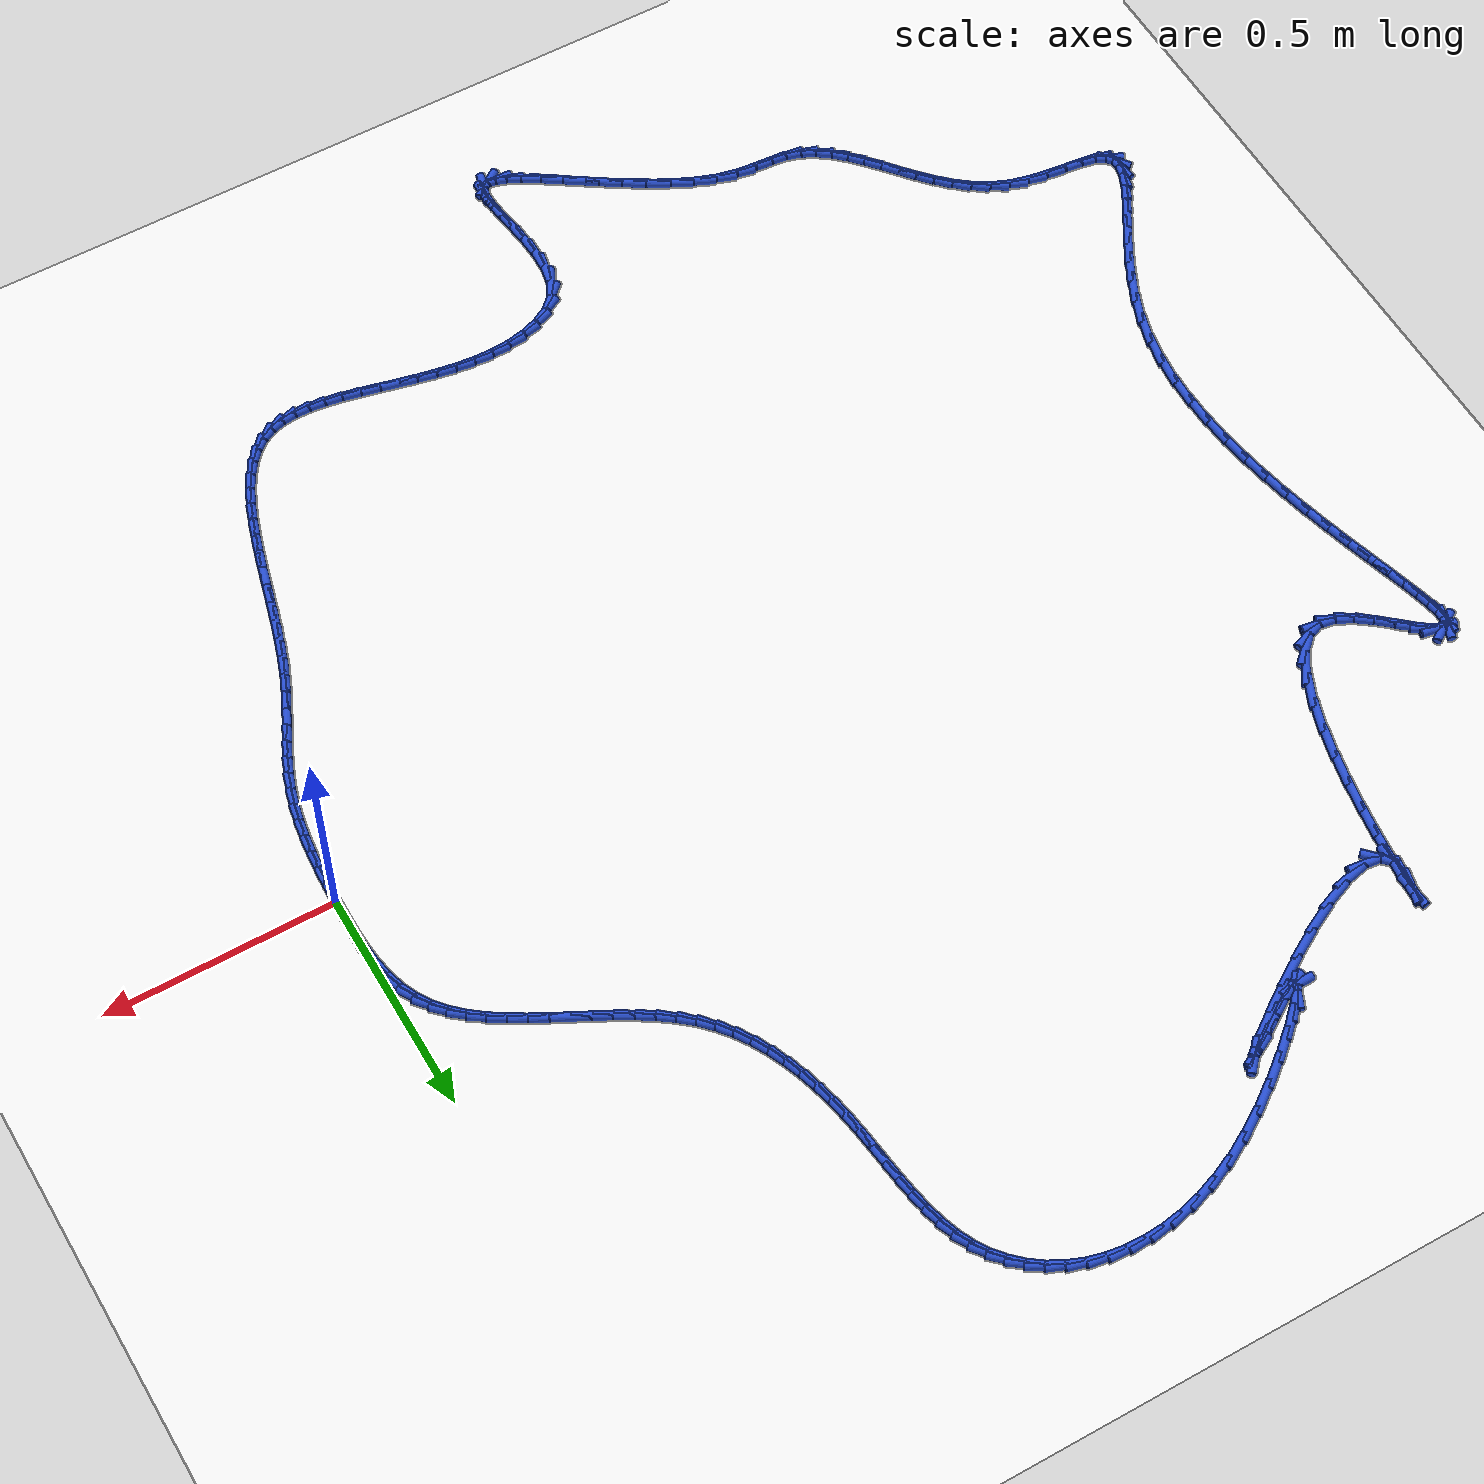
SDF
<sdf version="1.6">
 <world name="default">
  <light name="sun" type="directional">
   <pose>0 0 10 0 -0 0</pose>
   <diffuse>0.8 0.8 0.8 1</diffuse>
   <specular>0.2 0.2 0.2 1</specular>
   <attenuation>
    <range>1000</range>
    <constant>0.9</constant>
    <linear>0.01</linear>
    <quadratic>0.001</quadratic>
   </attenuation>
   <direction>-0.5 0.1 -0.9</direction>
  </light>
  <model name="ground_plane">
   <static>1</static>
   <link name="link">
    <collision name="collision">
     <geometry><plane><normal>0 0 1</normal><size>100 100</size></plane></geometry>
     <surface><friction><ode><mu>100</mu><mu2>50</mu2></ode></friction></surface>
    </collision>
    <visual name="visual">
     <cast_shadows>0</cast_shadows>
     <geometry><plane><normal>0 0 1</normal><size>100 100</size></plane></geometry>
     <material>
      <script><uri>file://media/materials/scripts/gazebo.material</uri><name>Gazebo/WhiteGlow</name></script>
     </material>
    </visual>
   </link>
  </model>
  <gravity>0 0 -9.8</gravity>
  <magnetic_field>6e-06 2.3e-05 -4.2e-05</magnetic_field>
  <atmosphere type="adiabatic"/>
  <physics name="default_physics" default="0" type="ode">
   <max_step_size>0.001</max_step_size>
   <real_time_factor>1</real_time_factor>
   <real_time_update_rate>1000</real_time_update_rate>
  </physics>
  <scene><ambient>0.4 0.4 0.4 1</ambient><background>0.7 0.7 0.7 1</background><shadows>1</shadows></scene>
  <spherical_coordinates>
   <surface_model>EARTH_WGS84</surface_model>
   <latitude_deg>0</latitude_deg>
   <longitude_deg>0</longitude_deg>
   <elevation>0</elevation>
   <heading_deg>0</heading_deg>
  </spherical_coordinates>
  <model name="line">
   <link name="link_0">
    <pose>4.0793106739767104e-18 0.0 0.01 0 1.57 1.5459125641176432</pose>
    <collision name="collision">
     <geometry><cylinder><radius>0.01</radius><length>0.08</length></cylinder></geometry>
    </collision>
    <visual name="visual">
     <material>
      <script><name>Gazebo/Blue</name><uri>file://media/materials/scripts/gazebo.material</uri></script>
     </material>
     <geometry><cylinder><radius>0.01</radius><length>0.08</length></cylinder></geometry>
    </visual>
   </link>
   <link name="link_1">
    <pose>0.0010174588526017984 0.04088002498099286 0.01 0 1.57 -1.5694775133342729</pose>
    <collision name="collision">
     <geometry><cylinder><radius>0.01</radius><length>0.08</length></cylinder></geometry>
    </collision>
    <visual name="visual">
     <material>
      <script><name>Gazebo/Blue</name><uri>file://media/materials/scripts/gazebo.material</uri></script>
     </material>
     <geometry><cylinder><radius>0.01</radius><length>0.08</length></cylinder></geometry>
    </visual>
   </link>
   <link name="link_2">
    <pose>0.0009635203807015269 0.08177924404384976 0.01 0 1.57 -1.5282282760953245</pose>
    <collision name="collision">
     <geometry><cylinder><radius>0.01</radius><length>0.08</length></cylinder></geometry>
    </collision>
    <visual name="visual">
     <material>
      <script><name>Gazebo/Blue</name><uri>file://media/materials/scripts/gazebo.material</uri></script>
     </material>
     <geometry><cylinder><radius>0.01</radius><length>0.08</length></cylinder></geometry>
    </visual>
   </link>
   <link name="link_3">
    <pose>-0.0007569286436015948 0.12217126803712974 0.01 0 1.57 -1.4699648799039942</pose>
    <collision name="collision">
     <geometry><cylinder><radius>0.01</radius><length>0.08</length></cylinder></geometry>
    </collision>
    <visual name="visual">
     <material>
      <script><name>Gazebo/Blue</name><uri>file://media/materials/scripts/gazebo.material</uri></script>
     </material>
     <geometry><cylinder><radius>0.01</radius><length>0.08</length></cylinder></geometry>
    </visual>
   </link>
   <link name="link_4">
    <pose>-0.004739001448208348 0.1615297078093917 0.01 0 1.57 -1.3918044302271575</pose>
    <collision name="collision">
     <geometry><cylinder><radius>0.01</radius><length>0.08</length></cylinder></geometry>
    </collision>
    <visual name="visual">
     <material>
      <script><name>Gazebo/Blue</name><uri>file://media/materials/scripts/gazebo.material</uri></script>
     </material>
     <geometry><cylinder><radius>0.01</radius><length>0.08</length></cylinder></geometry>
    </visual>
   </link>
   <link name="link_5">
    <pose>-0.011577811261019519 0.19932817420919463 0.01 0 1.57 -1.2902406140046252</pose>
    <collision name="collision">
     <geometry><cylinder><radius>0.01</radius><length>0.08</length></cylinder></geometry>
    </collision>
    <visual name="visual">
     <material>
      <script><name>Gazebo/Blue</name><uri>file://media/materials/scripts/gazebo.material</uri></script>
     </material>
     <geometry><cylinder><radius>0.01</radius><length>0.08</length></cylinder></geometry>
    </visual>
   </link>
   <link name="link_6">
    <pose>-0.0218684713099359 0.2350402780850974 0.01 0 1.57 -1.1620265997661303</pose>
    <collision name="collision">
     <geometry><cylinder><radius>0.01</radius><length>0.08</length></cylinder></geometry>
    </collision>
    <visual name="visual">
     <material>
      <script><name>Gazebo/Blue</name><uri>file://media/materials/scripts/gazebo.material</uri></script>
     </material>
     <geometry><cylinder><radius>0.01</radius><length>0.08</length></cylinder></geometry>
    </visual>
   </link>
   <link name="link_7">
    <pose>-0.036206094822858255 0.26813963028565907 0.01 0 1.57 -1.0119722392426187</pose>
    <collision name="collision">
     <geometry><cylinder><radius>0.01</radius><length>0.08</length></cylinder></geometry>
    </collision>
    <visual name="visual">
     <material>
      <script><name>Gazebo/Blue</name><uri>file://media/materials/scripts/gazebo.material</uri></script>
     </material>
     <geometry><cylinder><radius>0.01</radius><length>0.08</length></cylinder></geometry>
    </visual>
   </link>
   <link name="link_8">
    <pose>-0.0550229588782622 0.29823156113833743 0.01 0 1.57 -0.8715382130127898</pose>
    <collision name="collision">
     <geometry><cylinder><radius>0.01</radius><length>0.08</length></cylinder></geometry>
    </collision>
    <visual name="visual">
     <material>
      <script><name>Gazebo/Blue</name><uri>file://media/materials/scripts/gazebo.material</uri></script>
     </material>
     <geometry><cylinder><radius>0.01</radius><length>0.08</length></cylinder></geometry>
    </visual>
   </link>
   <link name="link_9">
    <pose>-0.07798858361329088 0.32553840123246996 0.01 0 1.57 -0.7536294902597601</pose>
    <collision name="collision">
     <geometry><cylinder><radius>0.01</radius><length>0.08</length></cylinder></geometry>
    </collision>
    <visual name="visual">
     <material>
      <script><name>Gazebo/Blue</name><uri>file://media/materials/scripts/gazebo.material</uri></script>
     </material>
     <geometry><cylinder><radius>0.01</radius><length>0.08</length></cylinder></geometry>
    </visual>
   </link>
   <link name="link_10">
    <pose>-0.1045493412333137 0.35046298732506265 0.01 0 1.57 -0.6593830718562225</pose>
    <collision name="collision">
     <geometry><cylinder><radius>0.01</radius><length>0.08</length></cylinder></geometry>
    </collision>
    <visual name="visual">
     <material>
      <script><name>Gazebo/Blue</name><uri>file://media/materials/scripts/gazebo.material</uri></script>
     </material>
     <geometry><cylinder><radius>0.01</radius><length>0.08</length></cylinder></geometry>
    </visual>
   </link>
   <link name="link_11">
    <pose>-0.1341515761600176 0.3734081786475668 0.01 0 1.57 -0.5874692081454452</pose>
    <collision name="collision">
     <geometry><cylinder><radius>0.01</radius><length>0.08</length></cylinder></geometry>
    </collision>
    <visual name="visual">
     <material>
      <script><name>Gazebo/Blue</name><uri>file://media/materials/scripts/gazebo.material</uri></script>
     </material>
     <geometry><cylinder><radius>0.01</radius><length>0.08</length></cylinder></geometry>
    </visual>
   </link>
   <link name="link_12">
    <pose>-0.16624163281508936 0.39477683443143397 0.01 0 1.57 -0.5356612256812052</pose>
    <collision name="collision">
     <geometry><cylinder><radius>0.01</radius><length>0.08</length></cylinder></geometry>
    </collision>
    <visual name="visual">
     <material>
      <script><name>Gazebo/Blue</name><uri>file://media/materials/scripts/gazebo.material</uri></script>
     </material>
     <geometry><cylinder><radius>0.01</radius><length>0.08</length></cylinder></geometry>
    </visual>
   </link>
   <link name="link_13">
    <pose>-0.20026585562021568 0.41497181390811555 0.01 0 1.57 -0.5017921582756374</pose>
    <collision name="collision">
     <geometry><cylinder><radius>0.01</radius><length>0.08</length></cylinder></geometry>
    </collision>
    <visual name="visual">
     <material>
      <script><name>Gazebo/Blue</name><uri>file://media/materials/scripts/gazebo.material</uri></script>
     </material>
     <geometry><cylinder><radius>0.01</radius><length>0.08</length></cylinder></geometry>
    </visual>
   </link>
   <link name="link_14">
    <pose>-0.23567058899708365 0.43439597630906335 0.01 0 1.57 -0.48419578139427033</pose>
    <collision name="collision">
     <geometry><cylinder><radius>0.01</radius><length>0.08</length></cylinder></geometry>
    </collision>
    <visual name="visual">
     <material>
      <script><name>Gazebo/Blue</name><uri>file://media/materials/scripts/gazebo.material</uri></script>
     </material>
     <geometry><cylinder><radius>0.01</radius><length>0.08</length></cylinder></geometry>
    </visual>
   </link>
   <link name="link_15">
    <pose>-0.2719021773673798 0.45345218086572864 0.01 0 1.57 -0.48185853467641737</pose>
    <collision name="collision">
     <geometry><cylinder><radius>0.01</radius><length>0.08</length></cylinder></geometry>
    </collision>
    <visual name="visual">
     <material>
      <script><name>Gazebo/Blue</name><uri>file://media/materials/scripts/gazebo.material</uri></script>
     </material>
     <geometry><cylinder><radius>0.01</radius><length>0.08</length></cylinder></geometry>
    </visual>
   </link>
   <link name="link_16">
    <pose>-0.30840696515279126 0.472543286809563 0.01 0 1.57 -0.49444323644424226</pose>
    <collision name="collision">
     <geometry><cylinder><radius>0.01</radius><length>0.08</length></cylinder></geometry>
    </collision>
    <visual name="visual">
     <material>
      <script><name>Gazebo/Blue</name><uri>file://media/materials/scripts/gazebo.material</uri></script>
     </material>
     <geometry><cylinder><radius>0.01</radius><length>0.08</length></cylinder></geometry>
    </visual>
   </link>
   <link name="link_17">
    <pose>-0.3446312967750047 0.4920721533720178 0.01 0 1.57 -0.5222612190505745</pose>
    <collision name="collision">
     <geometry><cylinder><radius>0.01</radius><length>0.08</length></cylinder></geometry>
    </collision>
    <visual name="visual">
     <material>
      <script><name>Gazebo/Blue</name><uri>file://media/materials/scripts/gazebo.material</uri></script>
     </material>
     <geometry><cylinder><radius>0.01</radius><length>0.08</length></cylinder></geometry>
    </visual>
   </link>
   <link name="link_18">
    <pose>-0.3800215166557068 0.5124416397845447 0.01 0 1.57 -0.5662065862711221</pose>
    <collision name="collision">
     <geometry><cylinder><radius>0.01</radius><length>0.08</length></cylinder></geometry>
    </collision>
    <visual name="visual">
     <material>
      <script><name>Gazebo/Blue</name><uri>file://media/materials/scripts/gazebo.material</uri></script>
     </material>
     <geometry><cylinder><radius>0.01</radius><length>0.08</length></cylinder></geometry>
    </visual>
   </link>
   <link name="link_19">
    <pose>-0.4140239692165846 0.534054605278595 0.01 0 1.57 -0.6276159613337432</pose>
    <collision name="collision">
     <geometry><cylinder><radius>0.01</radius><length>0.08</length></cylinder></geometry>
    </collision>
    <visual name="visual">
     <material>
      <script><name>Gazebo/Blue</name><uri>file://media/materials/scripts/gazebo.material</uri></script>
     </material>
     <geometry><cylinder><radius>0.01</radius><length>0.08</length></cylinder></geometry>
    </visual>
   </link>
   <link name="link_20">
    <pose>-0.44608499887932485 0.5573139090856203 0.01 0 1.57 -0.707967996527152</pose>
    <collision name="collision">
     <geometry><cylinder><radius>0.01</radius><length>0.08</length></cylinder></geometry>
    </collision>
    <visual name="visual">
     <material>
      <script><name>Gazebo/Blue</name><uri>file://media/materials/scripts/gazebo.material</uri></script>
     </material>
     <geometry><cylinder><radius>0.01</radius><length>0.08</length></cylinder></geometry>
    </visual>
   </link>
   <link name="link_21">
    <pose>-0.4756509500656144 0.5826224104370723 0.01 0 1.57 -0.8066006604199489</pose>
    <collision name="collision">
     <geometry><cylinder><radius>0.01</radius><length>0.08</length></cylinder></geometry>
    </collision>
    <visual name="visual">
     <material>
      <script><name>Gazebo/Blue</name><uri>file://media/materials/scripts/gazebo.material</uri></script>
     </material>
     <geometry><cylinder><radius>0.01</radius><length>0.08</length></cylinder></geometry>
    </visual>
   </link>
   <link name="link_22">
    <pose>-0.5022174997753895 0.6103400939409159 0.01 0 1.57 -0.9076254599743767</pose>
    <collision name="collision">
     <geometry><cylinder><radius>0.01</radius><length>0.08</length></cylinder></geometry>
    </collision>
    <visual name="visual">
     <material>
      <script><name>Gazebo/Blue</name><uri>file://media/materials/scripts/gazebo.material</uri></script>
     </material>
     <geometry><cylinder><radius>0.01</radius><length>0.08</length></cylinder></geometry>
    </visual>
   </link>
   <link name="link_23">
    <pose>-0.5257290914376277 0.6404369242150615 0.01 0 1.57 -1.0012967645038064</pose>
    <collision name="collision">
     <geometry><cylinder><radius>0.01</radius><length>0.08</length></cylinder></geometry>
    </collision>
    <visual name="visual">
     <material>
      <script><name>Gazebo/Blue</name><uri>file://media/materials/scripts/gazebo.material</uri></script>
     </material>
     <geometry><cylinder><radius>0.01</radius><length>0.08</length></cylinder></geometry>
    </visual>
   </link>
   <link name="link_24">
    <pose>-0.5463697206069192 0.6726746726802372 0.01 0 1.57 -1.0865871319223879</pose>
    <collision name="collision">
     <geometry><cylinder><radius>0.01</radius><length>0.08</length></cylinder></geometry>
    </collision>
    <visual name="visual">
     <material>
      <script><name>Gazebo/Blue</name><uri>file://media/materials/scripts/gazebo.material</uri></script>
     </material>
     <geometry><cylinder><radius>0.01</radius><length>0.08</length></cylinder></geometry>
    </visual>
   </link>
   <link name="link_25">
    <pose>-0.5643256303367371 0.7068131574704832 0.01 0 1.57 -1.163194079244653</pose>
    <collision name="collision">
     <geometry><cylinder><radius>0.01</radius><length>0.08</length></cylinder></geometry>
    </collision>
    <visual name="visual">
     <material>
      <script><name>Gazebo/Blue</name><uri>file://media/materials/scripts/gazebo.material</uri></script>
     </material>
     <geometry><cylinder><radius>0.01</radius><length>0.08</length></cylinder></geometry>
    </visual>
   </link>
   <link name="link_26">
    <pose>-0.579783063680555 0.7426121967198412 0.01 0 1.57 -1.2312902091395135</pose>
    <collision name="collision">
     <geometry><cylinder><radius>0.01</radius><length>0.08</length></cylinder></geometry>
    </collision>
    <visual name="visual">
     <material>
      <script><name>Gazebo/Blue</name><uri>file://media/materials/scripts/gazebo.material</uri></script>
     </material>
     <geometry><cylinder><radius>0.01</radius><length>0.08</length></cylinder></geometry>
    </visual>
   </link>
   <link name="link_27">
    <pose>-0.5929282636918456 0.779831608562351 0.01 0 1.57 -1.2913439107181948</pose>
    <collision name="collision">
     <geometry><cylinder><radius>0.01</radius><length>0.08</length></cylinder></geometry>
    </collision>
    <visual name="visual">
     <material>
      <script><name>Gazebo/Blue</name><uri>file://media/materials/scripts/gazebo.material</uri></script>
     </material>
     <geometry><cylinder><radius>0.01</radius><length>0.08</length></cylinder></geometry>
    </visual>
   </link>
   <link name="link_28">
    <pose>-0.6039474734240818 0.8182312111320537 0.01 0 1.57 -1.3439711569998176</pose>
    <collision name="collision">
     <geometry><cylinder><radius>0.01</radius><length>0.08</length></cylinder></geometry>
    </collision>
    <visual name="visual">
     <material>
      <script><name>Gazebo/Blue</name><uri>file://media/materials/scripts/gazebo.material</uri></script>
     </material>
     <geometry><cylinder><radius>0.01</radius><length>0.08</length></cylinder></geometry>
    </visual>
   </link>
   <link name="link_29">
    <pose>-0.613026935930737 0.8575708225629894 0.01 0 1.57 -1.389829488186364</pose>
    <collision name="collision">
     <geometry><cylinder><radius>0.01</radius><length>0.08</length></cylinder></geometry>
    </collision>
    <visual name="visual">
     <material>
      <script><name>Gazebo/Blue</name><uri>file://media/materials/scripts/gazebo.material</uri></script>
     </material>
     <geometry><cylinder><radius>0.01</radius><length>0.08</length></cylinder></geometry>
    </visual>
   </link>
   <link name="link_30">
    <pose>-0.6203528942652843 0.8976102609891994 0.01 0 1.57 -1.4286497479860152</pose>
    <collision name="collision">
     <geometry><cylinder><radius>0.01</radius><length>0.08</length></cylinder></geometry>
    </collision>
    <visual name="visual">
     <material>
      <script><name>Gazebo/Blue</name><uri>file://media/materials/scripts/gazebo.material</uri></script>
     </material>
     <geometry><cylinder><radius>0.01</radius><length>0.08</length></cylinder></geometry>
    </visual>
   </link>
   <link name="link_31">
    <pose>-0.6261477701496277 0.9381022201489617 0.01 0 1.57 -1.4544165192331961</pose>
    <collision name="collision">
     <geometry><cylinder><radius>0.01</radius><length>0.08</length></cylinder></geometry>
    </collision>
    <visual name="visual">
     <material>
      <script><name>Gazebo/Blue</name><uri>file://media/materials/scripts/gazebo.material</uri></script>
     </material>
     <geometry><cylinder><radius>0.01</radius><length>0.08</length></cylinder></geometry>
    </visual>
   </link>
   <link name="link_32">
    <pose>-0.6308994868947664 0.9787471105297207 0.01 0 1.57 -1.4645944888761098</pose>
    <collision name="collision">
     <geometry><cylinder><radius>0.01</radius><length>0.08</length></cylinder></geometry>
    </collision>
    <visual name="visual">
     <material>
      <script><name>Gazebo/Blue</name><uri>file://media/materials/scripts/gazebo.material</uri></script>
     </material>
     <geometry><cylinder><radius>0.01</radius><length>0.08</length></cylinder></geometry>
    </visual>
   </link>
   <link name="link_33">
    <pose>-0.6352142341851381 1.0192220533026923 0.01 0 1.57 -1.4590999739967583</pose>
    <collision name="collision">
     <geometry><cylinder><radius>0.01</radius><length>0.08</length></cylinder></geometry>
    </collision>
    <visual name="visual">
     <material>
      <script><name>Gazebo/Blue</name><uri>file://media/materials/scripts/gazebo.material</uri></script>
     </material>
     <geometry><cylinder><radius>0.01</radius><length>0.08</length></cylinder></geometry>
    </visual>
   </link>
   <link name="link_34">
    <pose>-0.63969874405213 1.0592040628387476 0.01 0 1.57 -1.4372700912046579</pose>
    <collision name="collision">
     <geometry><cylinder><radius>0.01</radius><length>0.08</length></cylinder></geometry>
    </collision>
    <visual name="visual">
     <material>
      <script><name>Gazebo/Blue</name><uri>file://media/materials/scripts/gazebo.material</uri></script>
     </material>
     <geometry><cylinder><radius>0.01</radius><length>0.08</length></cylinder></geometry>
    </visual>
   </link>
   <link name="link_35">
    <pose>-0.6449597485271279 1.0983701535087569 0.01 0 1.57 -1.3978192616607925</pose>
    <collision name="collision">
     <geometry><cylinder><radius>0.01</radius><length>0.08</length></cylinder></geometry>
    </collision>
    <visual name="visual">
     <material>
      <script><name>Gazebo/Blue</name><uri>file://media/materials/scripts/gazebo.material</uri></script>
     </material>
     <geometry><cylinder><radius>0.01</radius><length>0.08</length></cylinder></geometry>
    </visual>
   </link>
   <link name="link_36">
    <pose>-0.651603979641518 1.1363973396835902 0.01 0 1.57 -1.3389130899435444</pose>
    <collision name="collision">
     <geometry><cylinder><radius>0.01</radius><length>0.08</length></cylinder></geometry>
    </collision>
    <visual name="visual">
     <material>
      <script><name>Gazebo/Blue</name><uri>file://media/materials/scripts/gazebo.material</uri></script>
     </material>
     <geometry><cylinder><radius>0.01</radius><length>0.08</length></cylinder></geometry>
    </visual>
   </link>
   <link name="link_37">
    <pose>-0.6602381694266866 1.1729626357341183 0.01 0 1.57 -1.2584576142352395</pose>
    <collision name="collision">
     <geometry><cylinder><radius>0.01</radius><length>0.08</length></cylinder></geometry>
    </collision>
    <visual name="visual">
     <material>
      <script><name>Gazebo/Blue</name><uri>file://media/materials/scripts/gazebo.material</uri></script>
     </material>
     <geometry><cylinder><radius>0.01</radius><length>0.08</length></cylinder></geometry>
    </visual>
   </link>
   <link name="link_38">
    <pose>-0.6714690499140199 1.2077430560312115 0.01 0 1.57 -1.1547935067653148</pose>
    <collision name="collision">
     <geometry><cylinder><radius>0.01</radius><length>0.08</length></cylinder></geometry>
    </collision>
    <visual name="visual">
     <material>
      <script><name>Gazebo/Blue</name><uri>file://media/materials/scripts/gazebo.material</uri></script>
     </material>
     <geometry><cylinder><radius>0.01</radius><length>0.08</length></cylinder></geometry>
    </visual>
   </link>
   <link name="link_39">
    <pose>-0.6859033531349044 1.2404156149457408 0.01 0 1.57 -1.0295935186578848</pose>
    <collision name="collision">
     <geometry><cylinder><radius>0.01</radius><length>0.08</length></cylinder></geometry>
    </collision>
    <visual name="visual">
     <material>
      <script><name>Gazebo/Blue</name><uri>file://media/materials/scripts/gazebo.material</uri></script>
     </material>
     <geometry><cylinder><radius>0.01</radius><length>0.08</length></cylinder></geometry>
    </visual>
   </link>
   <link name="link_40">
    <pose>-0.7040839907762055 1.270662948343458 0.01 0 1.57 -0.8976465154691868</pose>
    <collision name="collision">
     <geometry><cylinder><radius>0.01</radius><length>0.08</length></cylinder></geometry>
    </collision>
    <visual name="visual">
     <material>
      <script><name>Gazebo/Blue</name><uri>file://media/materials/scripts/gazebo.material</uri></script>
     </material>
     <geometry><cylinder><radius>0.01</radius><length>0.08</length></cylinder></geometry>
    </visual>
   </link>
   <link name="link_41">
    <pose>-0.7260513970527477 1.298211951872143 0.01 0 1.57 -0.7662951952139173</pose>
    <collision name="collision">
     <geometry><cylinder><radius>0.01</radius><length>0.08</length></cylinder></geometry>
    </collision>
    <visual name="visual">
     <material>
      <script><name>Gazebo/Blue</name><uri>file://media/materials/scripts/gazebo.material</uri></script>
     </material>
     <geometry><cylinder><radius>0.01</radius><length>0.08</length></cylinder></geometry>
    </visual>
   </link>
   <link name="link_42">
    <pose>-0.7516081487189571 1.3228104724061214 0.01 0 1.57 -0.6365130016986633</pose>
    <collision name="collision">
     <geometry><cylinder><radius>0.01</radius><length>0.08</length></cylinder></geometry>
    </collision>
    <visual name="visual">
     <material>
      <script><name>Gazebo/Blue</name><uri>file://media/materials/scripts/gazebo.material</uri></script>
     </material>
     <geometry><cylinder><radius>0.01</radius><length>0.08</length></cylinder></geometry>
    </visual>
   </link>
   <link name="link_43">
    <pose>-0.7805554012860256 1.3442064820072537 0.01 0 1.57 -0.5091533271862781</pose>
    <collision name="collision">
     <geometry><cylinder><radius>0.01</radius><length>0.08</length></cylinder></geometry>
    </collision>
    <visual name="visual">
     <material>
      <script><name>Gazebo/Blue</name><uri>file://media/materials/scripts/gazebo.material</uri></script>
     </material>
     <geometry><cylinder><radius>0.01</radius><length>0.08</length></cylinder></geometry>
    </visual>
   </link>
   <link name="link_44">
    <pose>-0.8126943102651452 1.3621479527373985 0.01 0 1.57 -0.3849696056270498</pose>
    <collision name="collision">
     <geometry><cylinder><radius>0.01</radius><length>0.08</length></cylinder></geometry>
    </collision>
    <visual name="visual">
     <material>
      <script><name>Gazebo/Blue</name><uri>file://media/materials/scripts/gazebo.material</uri></script>
     </material>
     <geometry><cylinder><radius>0.01</radius><length>0.08</length></cylinder></geometry>
    </visual>
   </link>
   <link name="link_45">
    <pose>-0.8478260311675074 1.3763828566584162 0.01 0 1.57 -0.26460552125198344</pose>
    <collision name="collision">
     <geometry><cylinder><radius>0.01</radius><length>0.08</length></cylinder></geometry>
    </collision>
    <visual name="visual">
     <material>
      <script><name>Gazebo/Blue</name><uri>file://media/materials/scripts/gazebo.material</uri></script>
     </material>
     <geometry><cylinder><radius>0.01</radius><length>0.08</length></cylinder></geometry>
    </visual>
   </link>
   <link name="link_46">
    <pose>-0.8857517195043048 1.3866591658321665 0.01 0 1.57 -0.14858980268371746</pose>
    <collision name="collision">
     <geometry><cylinder><radius>0.01</radius><length>0.08</length></cylinder></geometry>
    </collision>
    <visual name="visual">
     <material>
      <script><name>Gazebo/Blue</name><uri>file://media/materials/scripts/gazebo.material</uri></script>
     </material>
     <geometry><cylinder><radius>0.01</radius><length>0.08</length></cylinder></geometry>
    </visual>
   </link>
   <link name="link_47">
    <pose>-0.9262725307867288 1.3927248523205087 0.01 0 1.57 -0.037334567592451025</pose>
    <collision name="collision">
     <geometry><cylinder><radius>0.01</radius><length>0.08</length></cylinder></geometry>
    </collision>
    <visual name="visual">
     <material>
      <script><name>Gazebo/Blue</name><uri>file://media/materials/scripts/gazebo.material</uri></script>
     </material>
     <geometry><cylinder><radius>0.01</radius><length>0.08</length></cylinder></geometry>
    </visual>
   </link>
   <link name="link_48">
    <pose>-0.9691896205259716 1.3943278881853034 0.01 0 1.57 0.06886302448914783</pose>
    <collision name="collision">
     <geometry><cylinder><radius>0.01</radius><length>0.08</length></cylinder></geometry>
    </collision>
    <visual name="visual">
     <material>
      <script><name>Gazebo/Blue</name><uri>file://media/materials/scripts/gazebo.material</uri></script>
     </material>
     <geometry><cylinder><radius>0.01</radius><length>0.08</length></cylinder></geometry>
    </visual>
   </link>
   <link name="link_49">
    <pose>-1.0143041442332248 1.39121624548841 0.01 0 1.57 0.16981570867951956</pose>
    <collision name="collision">
     <geometry><cylinder><radius>0.01</radius><length>0.08</length></cylinder></geometry>
    </collision>
    <visual name="visual">
     <material>
      <script><name>Gazebo/Blue</name><uri>file://media/materials/scripts/gazebo.material</uri></script>
     </material>
     <geometry><cylinder><radius>0.01</radius><length>0.08</length></cylinder></geometry>
    </visual>
   </link>
   <link name="link_50">
    <pose>-1.061417257419681 1.3831378962916885 0.01 0 1.57 0.26543767326882634</pose>
    <collision name="collision">
     <geometry><cylinder><radius>0.01</radius><length>0.08</length></cylinder></geometry>
    </collision>
    <visual name="visual">
     <material>
      <script><name>Gazebo/Blue</name><uri>file://media/materials/scripts/gazebo.material</uri></script>
     </material>
     <geometry><cylinder><radius>0.01</radius><length>0.08</length></cylinder></geometry>
    </visual>
   </link>
   <link name="link_51">
    <pose>-1.1103301155965313 1.3698408126569976 0.01 0 1.57 0.35573317610183175</pose>
    <collision name="collision">
     <geometry><cylinder><radius>0.01</radius><length>0.08</length></cylinder></geometry>
    </collision>
    <visual name="visual">
     <material>
      <script><name>Gazebo/Blue</name><uri>file://media/materials/scripts/gazebo.material</uri></script>
     </material>
     <geometry><cylinder><radius>0.01</radius><length>0.08</length></cylinder></geometry>
    </visual>
   </link>
   <link name="link_52">
    <pose>-1.1608438742749685 1.351072966646199 0.01 0 1.57 0.44078306069799317</pose>
    <collision name="collision">
     <geometry><cylinder><radius>0.01</radius><length>0.08</length></cylinder></geometry>
    </collision>
    <visual name="visual">
     <material>
      <script><name>Gazebo/Blue</name><uri>file://media/materials/scripts/gazebo.material</uri></script>
     </material>
     <geometry><cylinder><radius>0.01</radius><length>0.08</length></cylinder></geometry>
    </visual>
   </link>
   <link name="link_53">
    <pose>-1.212759688966184 1.3265823303211506 0.01 0 1.57 0.5195562922121968</pose>
    <collision name="collision">
     <geometry><cylinder><radius>0.01</radius><length>0.08</length></cylinder></geometry>
    </collision>
    <visual name="visual">
     <material>
      <script><name>Gazebo/Blue</name><uri>file://media/materials/scripts/gazebo.material</uri></script>
     </material>
     <geometry><cylinder><radius>0.01</radius><length>0.08</length></cylinder></geometry>
    </visual>
   </link>
   <link name="link_54">
    <pose>-1.2657705799792216 1.296261541887324 0.01 0 1.57 0.5830604110647526</pose>
    <collision name="collision">
     <geometry><cylinder><radius>0.01</radius><length>0.08</length></cylinder></geometry>
    </collision>
    <visual name="visual">
     <material>
      <script><name>Gazebo/Blue</name><uri>file://media/materials/scripts/gazebo.material</uri></script>
     </material>
     <geometry><cylinder><radius>0.01</radius><length>0.08</length></cylinder></geometry>
    </visual>
   </link>
   <link name="link_55">
    <pose>-1.3184268036266111 1.2615320595565362 0.01 0 1.57 0.6328845866517584</pose>
    <collision name="collision">
     <geometry><cylinder><radius>0.01</radius><length>0.08</length></cylinder></geometry>
    </collision>
    <visual name="visual">
     <material>
      <script><name>Gazebo/Blue</name><uri>file://media/materials/scripts/gazebo.material</uri></script>
     </material>
     <geometry><cylinder><radius>0.01</radius><length>0.08</length></cylinder></geometry>
    </visual>
   </link>
   <link name="link_56">
    <pose>-1.3685922306605784 1.2247336063615608 0.01 0 1.57 0.6759700859000737</pose>
    <collision name="collision">
     <geometry><cylinder><radius>0.01</radius><length>0.08</length></cylinder></geometry>
    </collision>
    <visual name="visual">
     <material>
      <script><name>Gazebo/Blue</name><uri>file://media/materials/scripts/gazebo.material</uri></script>
     </material>
     <geometry><cylinder><radius>0.01</radius><length>0.08</length></cylinder></geometry>
    </visual>
   </link>
   <link name="link_57">
    <pose>-1.4141213751803021 1.1882184229139683 0.01 0 1.57 0.7184749731573485</pose>
    <collision name="collision">
     <geometry><cylinder><radius>0.01</radius><length>0.08</length></cylinder></geometry>
    </collision>
    <visual name="visual">
     <material>
      <script><name>Gazebo/Blue</name><uri>file://media/materials/scripts/gazebo.material</uri></script>
     </material>
     <geometry><cylinder><radius>0.01</radius><length>0.08</length></cylinder></geometry>
    </visual>
   </link>
   <link name="link_58">
    <pose>-1.4528687512849614 1.154338749825329 0.01 0 1.57 0.769590123165994</pose>
    <collision name="collision">
     <geometry><cylinder><radius>0.01</radius><length>0.08</length></cylinder></geometry>
    </collision>
    <visual name="visual">
     <material>
      <script><name>Gazebo/Blue</name><uri>file://media/materials/scripts/gazebo.material</uri></script>
     </material>
     <geometry><cylinder><radius>0.01</radius><length>0.08</length></cylinder></geometry>
    </visual>
   </link>
   <link name="link_59">
    <pose>-1.4826888730737355 1.1254468277072123 0.01 0 1.57 0.854879111882033</pose>
    <collision name="collision">
     <geometry><cylinder><radius>0.01</radius><length>0.08</length></cylinder></geometry>
    </collision>
    <visual name="visual">
     <material>
      <script><name>Gazebo/Blue</name><uri>file://media/materials/scripts/gazebo.material</uri></script>
     </material>
     <geometry><cylinder><radius>0.01</radius><length>0.08</length></cylinder></geometry>
    </visual>
   </link>
   <link name="link_60">
    <pose>-1.5014362546458018 1.1038948971711888 0.01 0 1.57 1.1345410817419226</pose>
    <collision name="collision">
     <geometry><cylinder><radius>0.01</radius><length>0.08</length></cylinder></geometry>
    </collision>
    <visual name="visual">
     <material>
      <script><name>Gazebo/Blue</name><uri>file://media/materials/scripts/gazebo.material</uri></script>
     </material>
     <geometry><cylinder><radius>0.01</radius><length>0.08</length></cylinder></geometry>
    </visual>
   </link>
   <link name="link_61">
    <pose>-1.5069654101003405 1.0920351988288282 0.01 0 1.57 0.018786075864328632</pose>
    <collision name="collision">
     <geometry><cylinder><radius>0.01</radius><length>0.08</length></cylinder></geometry>
    </collision>
    <visual name="visual">
     <material>
      <script><name>Gazebo/Blue</name><uri>file://media/materials/scripts/gazebo.material</uri></script>
     </material>
     <geometry><cylinder><radius>0.01</radius><length>0.08</length></cylinder></geometry>
    </visual>
   </link>
   <link name="link_62">
    <pose>-1.4971308535365302 1.0922199732917006 0.01 0 1.57 0.4823575979765702</pose>
    <collision name="collision">
     <geometry><cylinder><radius>0.01</radius><length>0.08</length></cylinder></geometry>
    </collision>
    <visual name="visual">
     <material>
      <script><name>Gazebo/Blue</name><uri>file://media/materials/scripts/gazebo.material</uri></script>
     </material>
     <geometry><cylinder><radius>0.01</radius><length>0.08</length></cylinder></geometry>
    </visual>
   </link>
   <link name="link_63">
    <pose>-1.4706275743822779 1.1060973850619862 0.01 0 1.57 0.5562270535618038</pose>
    <collision name="collision">
     <geometry><cylinder><radius>0.01</radius><length>0.08</length></cylinder></geometry>
    </collision>
    <visual name="visual">
     <material>
      <script><name>Gazebo/Blue</name><uri>file://media/materials/scripts/gazebo.material</uri></script>
     </material>
     <geometry><cylinder><radius>0.01</radius><length>0.08</length></cylinder></geometry>
    </visual>
   </link>
   <link name="link_64">
    <pose>-1.433403098332669 1.1292400633540698 0.01 0 1.57 0.5761138794900177</pose>
    <collision name="collision">
     <geometry><cylinder><radius>0.01</radius><length>0.08</length></cylinder></geometry>
    </collision>
    <visual name="visual">
     <material>
      <script><name>Gazebo/Blue</name><uri>file://media/materials/scripts/gazebo.material</uri></script>
     </material>
     <geometry><cylinder><radius>0.01</radius><length>0.08</length></cylinder></geometry>
    </visual>
   </link>
   <link name="link_65">
    <pose>-1.3951128190272304 1.1541145126131491 0.01 0 1.57 0.570707777470858</pose>
    <collision name="collision">
     <geometry><cylinder><radius>0.01</radius><length>0.08</length></cylinder></geometry>
    </collision>
    <visual name="visual">
     <material>
      <script><name>Gazebo/Blue</name><uri>file://media/materials/scripts/gazebo.material</uri></script>
     </material>
     <geometry><cylinder><radius>0.01</radius><length>0.08</length></cylinder></geometry>
    </visual>
   </link>
   <link name="link_66">
    <pose>-1.3654419939996922 1.1731622199475367 0.01 0 1.57 0.47885668356282074</pose>
    <collision name="collision">
     <geometry><cylinder><radius>0.01</radius><length>0.08</length></cylinder></geometry>
    </collision>
    <visual name="visual">
     <material>
      <script><name>Gazebo/Blue</name><uri>file://media/materials/scripts/gazebo.material</uri></script>
     </material>
     <geometry><cylinder><radius>0.01</radius><length>0.08</length></cylinder></geometry>
    </visual>
   </link>
   <link name="link_67">
    <pose>-1.3532488192874783 1.1794924103885112 0.01 0 1.57 0.829918006784825</pose>
    <collision name="collision">
     <geometry><cylinder><radius>0.01</radius><length>0.08</length></cylinder></geometry>
    </collision>
    <visual name="visual">
     <material>
      <script><name>Gazebo/Blue</name><uri>file://media/materials/scripts/gazebo.material</uri></script>
     </material>
     <geometry><cylinder><radius>0.01</radius><length>0.08</length></cylinder></geometry>
    </visual>
   </link>
   <link name="link_68">
    <pose>-1.35975426115222 1.1723803171426823 0.01 0 1.57 0.6777075329046529</pose>
    <collision name="collision">
     <geometry><cylinder><radius>0.01</radius><length>0.08</length></cylinder></geometry>
    </collision>
    <visual name="visual">
     <material>
      <script><name>Gazebo/Blue</name><uri>file://media/materials/scripts/gazebo.material</uri></script>
     </material>
     <geometry><cylinder><radius>0.01</radius><length>0.08</length></cylinder></geometry>
    </visual>
   </link>
   <link name="link_69">
    <pose>-1.382052868286167 1.1544326856553333 0.01 0 1.57 0.639562951019323</pose>
    <collision name="collision">
     <geometry><cylinder><radius>0.01</radius><length>0.08</length></cylinder></geometry>
    </collision>
    <visual name="visual">
     <material>
      <script><name>Gazebo/Blue</name><uri>file://media/materials/scripts/gazebo.material</uri></script>
     </material>
     <geometry><cylinder><radius>0.01</radius><length>0.08</length></cylinder></geometry>
    </visual>
   </link>
   <link name="link_70">
    <pose>-1.4171988495770622 1.1282888301920768 0.01 0 1.57 0.6132166622590686</pose>
    <collision name="collision">
     <geometry><cylinder><radius>0.01</radius><length>0.08</length></cylinder></geometry>
    </collision>
    <visual name="visual">
     <material>
      <script><name>Gazebo/Blue</name><uri>file://media/materials/scripts/gazebo.material</uri></script>
     </material>
     <geometry><cylinder><radius>0.01</radius><length>0.08</length></cylinder></geometry>
    </visual>
   </link>
   <link name="link_71">
    <pose>-1.4622464139126476 1.0965880650185258 0.01 0 1.57 0.5873294278791967</pose>
    <collision name="collision">
     <geometry><cylinder><radius>0.01</radius><length>0.08</length></cylinder></geometry>
    </collision>
    <visual name="visual">
     <material>
      <script><name>Gazebo/Blue</name><uri>file://media/materials/scripts/gazebo.material</uri></script>
     </material>
     <geometry><cylinder><radius>0.01</radius><length>0.08</length></cylinder></geometry>
    </visual>
   </link>
   <link name="link_72">
    <pose>-1.5142497701806672 1.0619697044002923 0.01 0 1.57 0.557163939968873</pose>
    <collision name="collision">
     <geometry><cylinder><radius>0.01</radius><length>0.08</length></cylinder></geometry>
    </collision>
    <visual name="visual">
     <material>
      <script><name>Gazebo/Blue</name><uri>file://media/materials/scripts/gazebo.material</uri></script>
     </material>
     <geometry><cylinder><radius>0.01</radius><length>0.08</length></cylinder></geometry>
    </visual>
   </link>
   <link name="link_73">
    <pose>-1.570263127268862 1.0270730626029894 0.01 0 1.57 0.5180869836818354</pose>
    <collision name="collision">
     <geometry><cylinder><radius>0.01</radius><length>0.08</length></cylinder></geometry>
    </collision>
    <visual name="visual">
     <material>
      <script><name>Gazebo/Blue</name><uri>file://media/materials/scripts/gazebo.material</uri></script>
     </material>
     <geometry><cylinder><radius>0.01</radius><length>0.08</length></cylinder></geometry>
    </visual>
   </link>
   <link name="link_74">
    <pose>-1.6273406940649773 0.994537453892229 0.01 0 1.57 0.4627379797853526</pose>
    <collision name="collision">
     <geometry><cylinder><radius>0.01</radius><length>0.08</length></cylinder></geometry>
    </collision>
    <visual name="visual">
     <material>
      <script><name>Gazebo/Blue</name><uri>file://media/materials/scripts/gazebo.material</uri></script>
     </material>
     <geometry><cylinder><radius>0.01</radius><length>0.08</length></cylinder></geometry>
    </visual>
   </link>
   <link name="link_75">
    <pose>-1.6825366794567536 0.9670021925336243 0.01 0 1.57 0.3761885743820606</pose>
    <collision name="collision">
     <geometry><cylinder><radius>0.01</radius><length>0.08</length></cylinder></geometry>
    </collision>
    <visual name="visual">
     <material>
      <script><name>Gazebo/Blue</name><uri>file://media/materials/scripts/gazebo.material</uri></script>
     </material>
     <geometry><cylinder><radius>0.01</radius><length>0.08</length></cylinder></geometry>
    </visual>
   </link>
   <link name="link_76">
    <pose>-1.7329052923319341 0.9471065927927875 0.01 0 1.57 0.22204385169420318</pose>
    <collision name="collision">
     <geometry><cylinder><radius>0.01</radius><length>0.08</length></cylinder></geometry>
    </collision>
    <visual name="visual">
     <material>
      <script><name>Gazebo/Blue</name><uri>file://media/materials/scripts/gazebo.material</uri></script>
     </material>
     <geometry><cylinder><radius>0.01</radius><length>0.08</length></cylinder></geometry>
    </visual>
   </link>
   <link name="link_77">
    <pose>-1.775500741578263 0.9374899689353311 0.01 0 1.57 -0.10320880104079556</pose>
    <collision name="collision">
     <geometry><cylinder><radius>0.01</radius><length>0.08</length></cylinder></geometry>
    </collision>
    <visual name="visual">
     <material>
      <script><name>Gazebo/Blue</name><uri>file://media/materials/scripts/gazebo.material</uri></script>
     </material>
     <geometry><cylinder><radius>0.01</radius><length>0.08</length></cylinder></geometry>
    </visual>
   </link>
   <link name="link_78">
    <pose>-1.8073772360834823 0.9407916352268679 0.01 0 1.57 -0.8028634563644587</pose>
    <collision name="collision">
     <geometry><cylinder><radius>0.01</radius><length>0.08</length></cylinder></geometry>
    </collision>
    <visual name="visual">
     <material>
      <script><name>Gazebo/Blue</name><uri>file://media/materials/scripts/gazebo.material</uri></script>
     </material>
     <geometry><cylinder><radius>0.01</radius><length>0.08</length></cylinder></geometry>
    </visual>
   </link>
   <link name="link_79">
    <pose>-1.8255889847353346 0.9596509059330103 0.01 0 1.57 -1.5069426012306524</pose>
    <collision name="collision">
     <geometry><cylinder><radius>0.01</radius><length>0.08</length></cylinder></geometry>
    </collision>
    <visual name="visual">
     <material>
      <script><name>Gazebo/Blue</name><uri>file://media/materials/scripts/gazebo.material</uri></script>
     </material>
     <geometry><cylinder><radius>0.01</radius><length>0.08</length></cylinder></geometry>
    </visual>
   </link>
   <link name="link_80">
    <pose>-1.8278705154385124 0.9953329121556506 0.01 0 1.57 1.4436677827581392</pose>
    <collision name="collision">
     <geometry><cylinder><radius>0.01</radius><length>0.08</length></cylinder></geometry>
    </collision>
    <visual name="visual">
     <material>
      <script><name>Gazebo/Blue</name><uri>file://media/materials/scripts/gazebo.material</uri></script>
     </material>
     <geometry><cylinder><radius>0.01</radius><length>0.08</length></cylinder></geometry>
    </visual>
   </link>
   <link name="link_81">
    <pose>-1.8240726476049007 1.0250460330423465 0.01 0 1.57 1.328421006401657</pose>
    <collision name="collision">
     <geometry><cylinder><radius>0.01</radius><length>0.08</length></cylinder></geometry>
    </collision>
    <visual name="visual">
     <material>
      <script><name>Gazebo/Blue</name><uri>file://media/materials/scripts/gazebo.material</uri></script>
     </material>
     <geometry><cylinder><radius>0.01</radius><length>0.08</length></cylinder></geometry>
    </visual>
   </link>
   <link name="link_82">
    <pose>-1.8217979491536394 1.0342465573695097 0.01 0 1.57 -1.506038837583365</pose>
    <collision name="collision">
     <geometry><cylinder><radius>0.01</radius><length>0.08</length></cylinder></geometry>
    </collision>
    <visual name="visual">
     <material>
      <script><name>Gazebo/Blue</name><uri>file://media/materials/scripts/gazebo.material</uri></script>
     </material>
     <geometry><cylinder><radius>0.01</radius><length>0.08</length></cylinder></geometry>
    </visual>
   </link>
   <link name="link_83">
    <pose>-1.8212202264640514 1.0253377052123658 0.01 0 1.57 1.5208128409160766</pose>
    <collision name="collision">
     <geometry><cylinder><radius>0.01</radius><length>0.08</length></cylinder></geometry>
    </collision>
    <visual name="visual">
     <material>
      <script><name>Gazebo/Blue</name><uri>file://media/materials/scripts/gazebo.material</uri></script>
     </material>
     <geometry><cylinder><radius>0.01</radius><length>0.08</length></cylinder></geometry>
    </visual>
   </link>
   <link name="link_84">
    <pose>-1.8224437126826953 1.000880284347476 0.01 0 1.57 1.4874297601144753</pose>
    <collision name="collision">
     <geometry><cylinder><radius>0.01</radius><length>0.08</length></cylinder></geometry>
    </collision>
    <visual name="visual">
     <material>
      <script><name>Gazebo/Blue</name><uri>file://media/materials/scripts/gazebo.material</uri></script>
     </material>
     <geometry><cylinder><radius>0.01</radius><length>0.08</length></cylinder></geometry>
    </visual>
   </link>
   <link name="link_85">
    <pose>-1.8255726409561295 0.9634351025514017 0.01 0 1.57 1.4638655770725422</pose>
    <collision name="collision">
     <geometry><cylinder><radius>0.01</radius><length>0.08</length></cylinder></geometry>
    </collision>
    <visual name="visual">
     <material>
      <script><name>Gazebo/Blue</name><uri>file://media/materials/scripts/gazebo.material</uri></script>
     </material>
     <geometry><cylinder><radius>0.01</radius><length>0.08</length></cylinder></geometry>
    </visual>
   </link>
   <link name="link_86">
    <pose>-1.8307112444309124 0.9155629676007052 0.01 0 1.57 1.441406021894597</pose>
    <collision name="collision">
     <geometry><cylinder><radius>0.01</radius><length>0.08</length></cylinder></geometry>
    </collision>
    <visual name="visual">
     <material>
      <script><name>Gazebo/Blue</name><uri>file://media/materials/scripts/gazebo.material</uri></script>
     </material>
     <geometry><cylinder><radius>0.01</radius><length>0.08</length></cylinder></geometry>
    </visual>
   </link>
   <link name="link_87">
    <pose>-1.8379637562536026 0.8598246872719474 0.01 0 1.57 1.4168777724011747</pose>
    <collision name="collision">
     <geometry><cylinder><radius>0.01</radius><length>0.08</length></cylinder></geometry>
    </collision>
    <visual name="visual">
     <material>
      <script><name>Gazebo/Blue</name><uri>file://media/materials/scripts/gazebo.material</uri></script>
     </material>
     <geometry><cylinder><radius>0.01</radius><length>0.08</length></cylinder></geometry>
    </visual>
   </link>
   <link name="link_88">
    <pose>-1.8474344095707584 0.7987810693416887 0.01 0 1.57 1.387982483756194</pose>
    <collision name="collision">
     <geometry><cylinder><radius>0.01</radius><length>0.08</length></cylinder></geometry>
    </collision>
    <visual name="visual">
     <material>
      <script><name>Gazebo/Blue</name><uri>file://media/materials/scripts/gazebo.material</uri></script>
     </material>
     <geometry><cylinder><radius>0.01</radius><length>0.08</length></cylinder></geometry>
    </visual>
   </link>
   <link name="link_89">
    <pose>-1.8592274375289373 0.7349929215864922 0.01 0 1.57 1.3520727916070092</pose>
    <collision name="collision">
     <geometry><cylinder><radius>0.01</radius><length>0.08</length></cylinder></geometry>
    </collision>
    <visual name="visual">
     <material>
      <script><name>Gazebo/Blue</name><uri>file://media/materials/scripts/gazebo.material</uri></script>
     </material>
     <geometry><cylinder><radius>0.01</radius><length>0.08</length></cylinder></geometry>
    </visual>
   </link>
   <link name="link_90">
    <pose>-1.8734470732746995 0.6710210517829182 0.01 0 1.57 1.3052712809088163</pose>
    <collision name="collision">
     <geometry><cylinder><radius>0.01</radius><length>0.08</length></cylinder></geometry>
    </collision>
    <visual name="visual">
     <material>
      <script><name>Gazebo/Blue</name><uri>file://media/materials/scripts/gazebo.material</uri></script>
     </material>
     <geometry><cylinder><radius>0.01</radius><length>0.08</length></cylinder></geometry>
    </visual>
   </link>
   <link name="link_91">
    <pose>-1.8901975499546018 0.6094262677075293 0.01 0 1.57 1.2411256188801065</pose>
    <collision name="collision">
     <geometry><cylinder><radius>0.01</radius><length>0.08</length></cylinder></geometry>
    </collision>
    <visual name="visual">
     <material>
      <script><name>Gazebo/Blue</name><uri>file://media/materials/scripts/gazebo.material</uri></script>
     </material>
     <geometry><cylinder><radius>0.01</radius><length>0.08</length></cylinder></geometry>
    </visual>
   </link>
   <link name="link_92">
    <pose>-1.9095831007152042 0.5527693771368855 0.01 0 1.57 1.1478802701288995</pose>
    <collision name="collision">
     <geometry><cylinder><radius>0.01</radius><length>0.08</length></cylinder></geometry>
    </collision>
    <visual name="visual">
     <material>
      <script><name>Gazebo/Blue</name><uri>file://media/materials/scripts/gazebo.material</uri></script>
     </material>
     <geometry><cylinder><radius>0.01</radius><length>0.08</length></cylinder></geometry>
    </visual>
   </link>
   <link name="link_93">
    <pose>-1.9317079587030639 0.5036111878475498 0.01 0 1.57 1.002477298806502</pose>
    <collision name="collision">
     <geometry><cylinder><radius>0.01</radius><length>0.08</length></cylinder></geometry>
    </collision>
    <visual name="visual">
     <material>
      <script><name>Gazebo/Blue</name><uri>file://media/materials/scripts/gazebo.material</uri></script>
     </material>
     <geometry><cylinder><radius>0.01</radius><length>0.08</length></cylinder></geometry>
    </visual>
   </link>
   <link name="link_94">
    <pose>-1.9566763570647396 0.4645125076160823 0.01 0 1.57 0.7589713587241775</pose>
    <collision name="collision">
     <geometry><cylinder><radius>0.01</radius><length>0.08</length></cylinder></geometry>
    </collision>
    <visual name="visual">
     <material>
      <script><name>Gazebo/Blue</name><uri>file://media/materials/scripts/gazebo.material</uri></script>
     </material>
     <geometry><cylinder><radius>0.01</radius><length>0.08</length></cylinder></geometry>
    </visual>
   </link>
   <link name="link_95">
    <pose>-1.98459252894679 0.43803414421904563 0.01 0 1.57 0.34979970310285424</pose>
    <collision name="collision">
     <geometry><cylinder><radius>0.01</radius><length>0.08</length></cylinder></geometry>
    </collision>
    <visual name="visual">
     <material>
      <script><name>Gazebo/Blue</name><uri>file://media/materials/scripts/gazebo.material</uri></script>
     </material>
     <geometry><cylinder><radius>0.01</radius><length>0.08</length></cylinder></geometry>
    </visual>
   </link>
   <link name="link_96">
    <pose>-2.0155607074957738 0.42673690543300047 0.01 0 1.57 -0.1526729323194739</pose>
    <collision name="collision">
     <geometry><cylinder><radius>0.01</radius><length>0.08</length></cylinder></geometry>
    </collision>
    <visual name="visual">
     <material>
      <script><name>Gazebo/Blue</name><uri>file://media/materials/scripts/gazebo.material</uri></script>
     </material>
     <geometry><cylinder><radius>0.01</radius><length>0.08</length></cylinder></geometry>
    </visual>
   </link>
   <link name="link_97">
    <pose>-2.0493783749105563 0.43194044062244885 0.01 0 1.57 -0.4702387831808139</pose>
    <collision name="collision">
     <geometry><cylinder><radius>0.01</radius><length>0.08</length></cylinder></geometry>
    </collision>
    <visual name="visual">
     <material>
      <script><name>Gazebo/Blue</name><uri>file://media/materials/scripts/gazebo.material</uri></script>
     </material>
     <geometry><cylinder><radius>0.01</radius><length>0.08</length></cylinder></geometry>
    </visual>
   </link>
   <link name="link_98">
    <pose>-2.0845738313068907 0.44982910607211296 0.01 0 1.57 -0.631433915418022</pose>
    <collision name="collision">
     <geometry><cylinder><radius>0.01</radius><length>0.08</length></cylinder></geometry>
    </collision>
    <visual name="visual">
     <material>
      <script><name>Gazebo/Blue</name><uri>file://media/materials/scripts/gazebo.material</uri></script>
     </material>
     <geometry><cylinder><radius>0.01</radius><length>0.08</length></cylinder></geometry>
    </visual>
   </link>
   <link name="link_99">
    <pose>-2.119347176751233 0.475259313507504 0.01 0 1.57 -0.7073323193499907</pose>
    <collision name="collision">
     <geometry><cylinder><radius>0.01</radius><length>0.08</length></cylinder></geometry>
    </collision>
    <visual name="visual">
     <material>
      <script><name>Gazebo/Blue</name><uri>file://media/materials/scripts/gazebo.material</uri></script>
     </material>
     <geometry><cylinder><radius>0.01</radius><length>0.08</length></cylinder></geometry>
    </visual>
   </link>
   <link name="link_100">
    <pose>-2.1518985108563737 0.5030874728185336 0.01 0 1.57 -0.7211929996308618</pose>
    <collision name="collision">
     <geometry><cylinder><radius>0.01</radius><length>0.08</length></cylinder></geometry>
    </collision>
    <visual name="visual">
     <material>
      <script><name>Gazebo/Blue</name><uri>file://media/materials/scripts/gazebo.material</uri></script>
     </material>
     <geometry><cylinder><radius>0.01</radius><length>0.08</length></cylinder></geometry>
    </visual>
   </link>
   <link name="link_101">
    <pose>-2.1804279332351038 0.5281699938951148 0.01 0 1.57 -0.6603225205348383</pose>
    <collision name="collision">
     <geometry><cylinder><radius>0.01</radius><length>0.08</length></cylinder></geometry>
    </collision>
    <visual name="visual">
     <material>
      <script><name>Gazebo/Blue</name><uri>file://media/materials/scripts/gazebo.material</uri></script>
     </material>
     <geometry><cylinder><radius>0.01</radius><length>0.08</length></cylinder></geometry>
    </visual>
   </link>
   <link name="link_102">
    <pose>-2.203397338243139 0.5460085352333544 0.01 0 1.57 -0.5118759057970284</pose>
    <collision name="collision">
     <geometry><cylinder><radius>0.01</radius><length>0.08</length></cylinder></geometry>
    </collision>
    <visual name="visual">
     <material>
      <script><name>Gazebo/Blue</name><uri>file://media/materials/scripts/gazebo.material</uri></script>
     </material>
     <geometry><cylinder><radius>0.01</radius><length>0.08</length></cylinder></geometry>
    </visual>
   </link>
   <link name="link_103">
    <pose>-2.220750919686945 0.5557581963567413 0.01 0 1.57 -0.17044051881066927</pose>
    <collision name="collision">
     <geometry><cylinder><radius>0.01</radius><length>0.08</length></cylinder></geometry>
    </collision>
    <visual name="visual">
     <material>
      <script><name>Gazebo/Blue</name><uri>file://media/materials/scripts/gazebo.material</uri></script>
     </material>
     <geometry><cylinder><radius>0.01</radius><length>0.08</length></cylinder></geometry>
    </visual>
   </link>
   <link name="link_104">
    <pose>-2.2329539843655257 0.5578584701587285 0.01 0 1.57 0.5967832256474492</pose>
    <collision name="collision">
     <geometry><cylinder><radius>0.01</radius><length>0.08</length></cylinder></geometry>
    </collision>
    <visual name="visual">
     <material>
      <script><name>Gazebo/Blue</name><uri>file://media/materials/scripts/gazebo.material</uri></script>
     </material>
     <geometry><cylinder><radius>0.01</radius><length>0.08</length></cylinder></geometry>
    </visual>
   </link>
   <link name="link_105">
    <pose>-2.2404724127503903 0.5527502634701962 0.01 0 1.57 1.2997834457611077</pose>
    <collision name="collision">
     <geometry><cylinder><radius>0.01</radius><length>0.08</length></cylinder></geometry>
    </collision>
    <visual name="visual">
     <material>
      <script><name>Gazebo/Blue</name><uri>file://media/materials/scripts/gazebo.material</uri></script>
     </material>
     <geometry><cylinder><radius>0.01</radius><length>0.08</length></cylinder></geometry>
    </visual>
   </link>
   <link name="link_106">
    <pose>-2.24377208531305 0.5408744831220241 0.01 0 1.57 -1.5459035653549602</pose>
    <collision name="collision">
     <geometry><cylinder><radius>0.01</radius><length>0.08</length></cylinder></geometry>
    </collision>
    <visual name="visual">
     <material>
      <script><name>Gazebo/Blue</name><uri>file://media/materials/scripts/gazebo.material</uri></script>
     </material>
     <geometry><cylinder><radius>0.01</radius><length>0.08</length></cylinder></geometry>
    </visual>
   </link>
   <link name="link_107">
    <pose>-2.243318882525013 0.5226720359450925 0.01 0 1.57 -1.4167554907817101</pose>
    <collision name="collision">
     <geometry><cylinder><radius>0.01</radius><length>0.08</length></cylinder></geometry>
    </collision>
    <visual name="visual">
     <material>
      <script><name>Gazebo/Blue</name><uri>file://media/materials/scripts/gazebo.material</uri></script>
     </material>
     <geometry><cylinder><radius>0.01</radius><length>0.08</length></cylinder></geometry>
    </visual>
   </link>
   <link name="link_108">
    <pose>-2.2395786848577903 0.49858382877028073 0.01 0 1.57 -1.3521786931285824</pose>
    <collision name="collision">
     <geometry><cylinder><radius>0.01</radius><length>0.08</length></cylinder></geometry>
    </collision>
    <visual name="visual">
     <material>
      <script><name>Gazebo/Blue</name><uri>file://media/materials/scripts/gazebo.material</uri></script>
     </material>
     <geometry><cylinder><radius>0.01</radius><length>0.08</length></cylinder></geometry>
    </visual>
   </link>
   <link name="link_109">
    <pose>-2.233017372782893 0.4690507684284695 0.01 0 1.57 -1.3181397086267796</pose>
    <collision name="collision">
     <geometry><cylinder><radius>0.01</radius><length>0.08</length></cylinder></geometry>
    </collision>
    <visual name="visual">
     <material>
      <script><name>Gazebo/Blue</name><uri>file://media/materials/scripts/gazebo.material</uri></script>
     </material>
     <geometry><cylinder><radius>0.01</radius><length>0.08</length></cylinder></geometry>
    </visual>
   </link>
   <link name="link_110">
    <pose>-2.224100826771829 0.4345137617505381 0.01 0 1.57 -1.301161168196966</pose>
    <collision name="collision">
     <geometry><cylinder><radius>0.01</radius><length>0.08</length></cylinder></geometry>
    </collision>
    <visual name="visual">
     <material>
      <script><name>Gazebo/Blue</name><uri>file://media/materials/scripts/gazebo.material</uri></script>
     </material>
     <geometry><cylinder><radius>0.01</radius><length>0.08</length></cylinder></geometry>
    </visual>
   </link>
   <link name="link_111">
    <pose>-2.21329492729611 0.3954137155673669 0.01 0 1.57 -1.295061538411857</pose>
    <collision name="collision">
     <geometry><cylinder><radius>0.01</radius><length>0.08</length></cylinder></geometry>
    </collision>
    <visual name="visual">
     <material>
      <script><name>Gazebo/Blue</name><uri>file://media/materials/scripts/gazebo.material</uri></script>
     </material>
     <geometry><cylinder><radius>0.01</radius><length>0.08</length></cylinder></geometry>
    </visual>
   </link>
   <link name="link_112">
    <pose>-2.201065554827246 0.3521915367098353 0.01 0 1.57 -1.296720110162653</pose>
    <collision name="collision">
     <geometry><cylinder><radius>0.01</radius><length>0.08</length></cylinder></geometry>
    </collision>
    <visual name="visual">
     <material>
      <script><name>Gazebo/Blue</name><uri>file://media/materials/scripts/gazebo.material</uri></script>
     </material>
     <geometry><cylinder><radius>0.01</radius><length>0.08</length></cylinder></geometry>
    </visual>
   </link>
   <link name="link_113">
    <pose>-2.1878785898367457 0.30528813200882415 0.01 0 1.57 -1.304486438759034</pose>
    <collision name="collision">
     <geometry><cylinder><radius>0.01</radius><length>0.08</length></cylinder></geometry>
    </collision>
    <visual name="visual">
     <material>
      <script><name>Gazebo/Blue</name><uri>file://media/materials/scripts/gazebo.material</uri></script>
     </material>
     <geometry><cylinder><radius>0.01</radius><length>0.08</length></cylinder></geometry>
    </visual>
   </link>
   <link name="link_114">
    <pose>-2.17419991279612 0.25514440829521223 0.01 0 1.57 -1.317502602987457</pose>
    <collision name="collision">
     <geometry><cylinder><radius>0.01</radius><length>0.08</length></cylinder></geometry>
    </collision>
    <visual name="visual">
     <material>
      <script><name>Gazebo/Blue</name><uri>file://media/materials/scripts/gazebo.material</uri></script>
     </material>
     <geometry><cylinder><radius>0.01</radius><length>0.08</length></cylinder></geometry>
    </visual>
   </link>
   <link name="link_115">
    <pose>-2.1604954041768787 0.20220127239988092 0.01 0 1.57 -1.3353870074837655</pose>
    <collision name="collision">
     <geometry><cylinder><radius>0.01</radius><length>0.08</length></cylinder></geometry>
    </collision>
    <visual name="visual">
     <material>
      <script><name>Gazebo/Blue</name><uri>file://media/materials/scripts/gazebo.material</uri></script>
     </material>
     <geometry><cylinder><radius>0.01</radius><length>0.08</length></cylinder></geometry>
    </visual>
   </link>
   <link name="link_116">
    <pose>-2.1472309444505315 0.1468996311537093 0.01 0 1.57 -1.3580783287999645</pose>
    <collision name="collision">
     <geometry><cylinder><radius>0.01</radius><length>0.08</length></cylinder></geometry>
    </collision>
    <visual name="visual">
     <material>
      <script><name>Gazebo/Blue</name><uri>file://media/materials/scripts/gazebo.material</uri></script>
     </material>
     <geometry><cylinder><radius>0.01</radius><length>0.08</length></cylinder></geometry>
    </visual>
   </link>
   <link name="link_117">
    <pose>-2.1348724140885897 0.08968039138757608 0.01 0 1.57 -1.3857572621649352</pose>
    <collision name="collision">
     <geometry><cylinder><radius>0.01</radius><length>0.08</length></cylinder></geometry>
    </collision>
    <visual name="visual">
     <material>
      <script><name>Gazebo/Blue</name><uri>file://media/materials/scripts/gazebo.material</uri></script>
     </material>
     <geometry><cylinder><radius>0.01</radius><length>0.08</length></cylinder></geometry>
    </visual>
   </link>
   <link name="link_118">
    <pose>-2.1238856935625616 0.030984459932363886 0.01 0 1.57 -1.4188088414333546</pose>
    <collision name="collision">
     <geometry><cylinder><radius>0.01</radius><length>0.08</length></cylinder></geometry>
    </collision>
    <visual name="visual">
     <material>
      <script><name>Gazebo/Blue</name><uri>file://media/materials/scripts/gazebo.material</uri></script>
     </material>
     <geometry><cylinder><radius>0.01</radius><length>0.08</length></cylinder></geometry>
    </visual>
   </link>
   <link name="link_119">
    <pose>-2.1147366633439586 -0.02874725638104872 0.01 0 1.57 -1.4578063050962744</pose>
    <collision name="collision">
     <geometry><cylinder><radius>0.01</radius><length>0.08</length></cylinder></geometry>
    </collision>
    <visual name="visual">
     <material>
      <script><name>Gazebo/Blue</name><uri>file://media/materials/scripts/gazebo.material</uri></script>
     </material>
     <geometry><cylinder><radius>0.01</radius><length>0.08</length></cylinder></geometry>
    </visual>
   </link>
   <link name="link_120">
    <pose>-2.1078912039042903 -0.08907385072178167 0.01 0 1.57 -1.503504396519858</pose>
    <collision name="collision">
     <geometry><cylinder><radius>0.01</radius><length>0.08</length></cylinder></geometry>
    </collision>
    <visual name="visual">
     <material>
      <script><name>Gazebo/Blue</name><uri>file://media/materials/scripts/gazebo.material</uri></script>
     </material>
     <geometry><cylinder><radius>0.01</radius><length>0.08</length></cylinder></geometry>
    </visual>
   </link>
   <link name="link_121">
    <pose>-2.1038151957150664 -0.14955441625895513 0.01 0 1.57 -1.5568310315354534</pose>
    <collision name="collision">
     <geometry><cylinder><radius>0.01</radius><length>0.08</length></cylinder></geometry>
    </collision>
    <visual name="visual">
     <material>
      <script><name>Gazebo/Blue</name><uri>file://media/materials/scripts/gazebo.material</uri></script>
     </material>
     <geometry><cylinder><radius>0.01</radius><length>0.08</length></cylinder></geometry>
    </visual>
   </link>
   <link name="link_122">
    <pose>-2.1029745192477973 -0.20974804616169077 0.01 0 1.57 1.5227294887673462</pose>
    <collision name="collision">
     <geometry><cylinder><radius>0.01</radius><length>0.08</length></cylinder></geometry>
    </collision>
    <visual name="visual">
     <material>
      <script><name>Gazebo/Blue</name><uri>file://media/materials/scripts/gazebo.material</uri></script>
     </material>
     <geometry><cylinder><radius>0.01</radius><length>0.08</length></cylinder></geometry>
    </visual>
   </link>
   <link name="link_123">
    <pose>-2.1058350549739924 -0.26921383359910533 0.01 0 1.57 1.4508265888066054</pose>
    <collision name="collision">
     <geometry><cylinder><radius>0.01</radius><length>0.08</length></cylinder></geometry>
    </collision>
    <visual name="visual">
     <material>
      <script><name>Gazebo/Blue</name><uri>file://media/materials/scripts/gazebo.material</uri></script>
     </material>
     <geometry><cylinder><radius>0.01</radius><length>0.08</length></cylinder></geometry>
    </visual>
   </link>
   <link name="link_124">
    <pose>-2.1128626833651625 -0.3275108717403207 0.01 0 1.57 1.3679259343271106</pose>
    <collision name="collision">
     <geometry><cylinder><radius>0.01</radius><length>0.08</length></cylinder></geometry>
    </collision>
    <visual name="visual">
     <material>
      <script><name>Gazebo/Blue</name><uri>file://media/materials/scripts/gazebo.material</uri></script>
     </material>
     <geometry><cylinder><radius>0.01</radius><length>0.08</length></cylinder></geometry>
    </visual>
   </link>
   <link name="link_125">
    <pose>-2.124523284892817 -0.3841982537544567 0.01 0 1.57 1.2745959543421672</pose>
    <collision name="collision">
     <geometry><cylinder><radius>0.01</radius><length>0.08</length></cylinder></geometry>
    </collision>
    <visual name="visual">
     <material>
      <script><name>Gazebo/Blue</name><uri>file://media/materials/scripts/gazebo.material</uri></script>
     </material>
     <geometry><cylinder><radius>0.01</radius><length>0.08</length></cylinder></geometry>
    </visual>
   </link>
   <link name="link_126">
    <pose>-2.141199902996702 -0.43884381524841887 0.01 0 1.57 1.1883047163483496</pose>
    <collision name="collision">
     <geometry><cylinder><radius>0.01</radius><length>0.08</length></cylinder></geometry>
    </collision>
    <visual name="visual">
     <material>
      <script><name>Gazebo/Blue</name><uri>file://media/materials/scripts/gazebo.material</uri></script>
     </material>
     <geometry><cylinder><radius>0.01</radius><length>0.08</length></cylinder></geometry>
    </visual>
   </link>
   <link name="link_127">
    <pose>-2.1622330383114146 -0.4911254194993059 0.01 0 1.57 1.1204038438040944</pose>
    <collision name="collision">
     <geometry><cylinder><radius>0.01</radius><length>0.08</length></cylinder></geometry>
    </collision>
    <visual name="visual">
     <material>
      <script><name>Gazebo/Blue</name><uri>file://media/materials/scripts/gazebo.material</uri></script>
     </material>
     <geometry><cylinder><radius>0.01</radius><length>0.08</length></cylinder></geometry>
    </visual>
   </link>
   <link name="link_128">
    <pose>-2.1862507689394426 -0.5407961172882902 0.01 0 1.57 1.0701082917032407</pose>
    <collision name="collision">
     <geometry><cylinder><radius>0.01</radius><length>0.08</length></cylinder></geometry>
    </collision>
    <visual name="visual">
     <material>
      <script><name>Gazebo/Blue</name><uri>file://media/materials/scripts/gazebo.material</uri></script>
     </material>
     <geometry><cylinder><radius>0.01</radius><length>0.08</length></cylinder></geometry>
    </visual>
   </link>
   <link name="link_129">
    <pose>-2.2118673751948403 -0.5876104155847275 0.01 0 1.57 1.0370931501255263</pose>
    <collision name="collision">
     <geometry><cylinder><radius>0.01</radius><length>0.08</length></cylinder></geometry>
    </collision>
    <visual name="visual">
     <material>
      <script><name>Gazebo/Blue</name><uri>file://media/materials/scripts/gazebo.material</uri></script>
     </material>
     <geometry><cylinder><radius>0.01</radius><length>0.08</length></cylinder></geometry>
    </visual>
   </link>
   <link name="link_130">
    <pose>-2.2376971373916668 -0.631322821357973 0.01 0 1.57 1.0224329840297177</pose>
    <collision name="collision">
     <geometry><cylinder><radius>0.01</radius><length>0.08</length></cylinder></geometry>
    </collision>
    <visual name="visual">
     <material>
      <script><name>Gazebo/Blue</name><uri>file://media/materials/scripts/gazebo.material</uri></script>
     </material>
     <geometry><cylinder><radius>0.01</radius><length>0.08</length></cylinder></geometry>
    </visual>
   </link>
   <link name="link_131">
    <pose>-2.2623543358439795 -0.6716878415773834 0.01 0 1.57 1.0296646743495128</pose>
    <collision name="collision">
     <geometry><cylinder><radius>0.01</radius><length>0.08</length></cylinder></geometry>
    </collision>
    <visual name="visual">
     <material>
      <script><name>Gazebo/Blue</name><uri>file://media/materials/scripts/gazebo.material</uri></script>
     </material>
     <geometry><cylinder><radius>0.01</radius><length>0.08</length></cylinder></geometry>
    </visual>
   </link>
   <link name="link_132">
    <pose>-2.2844532508658335 -0.708459983212312 0.01 0 1.57 1.0669899431658216</pose>
    <collision name="collision">
     <geometry><cylinder><radius>0.01</radius><length>0.08</length></cylinder></geometry>
    </collision>
    <visual name="visual">
     <material>
      <script><name>Gazebo/Blue</name><uri>file://media/materials/scripts/gazebo.material</uri></script>
     </material>
     <geometry><cylinder><radius>0.01</radius><length>0.08</length></cylinder></geometry>
    </visual>
   </link>
   <link name="link_133">
    <pose>-2.302608162771287 -0.7413937532321153 0.01 0 1.57 1.1524849078441046</pose>
    <collision name="collision">
     <geometry><cylinder><radius>0.01</radius><length>0.08</length></cylinder></geometry>
    </collision>
    <visual name="visual">
     <material>
      <script><name>Gazebo/Blue</name><uri>file://media/materials/scripts/gazebo.material</uri></script>
     </material>
     <geometry><cylinder><radius>0.01</radius><length>0.08</length></cylinder></geometry>
    </visual>
   </link>
   <link name="link_134">
    <pose>-2.3154333518743977 -0.7702436586061489 0.01 0 1.57 1.3266004614899507</pose>
    <collision name="collision">
     <geometry><cylinder><radius>0.01</radius><length>0.08</length></cylinder></geometry>
    </collision>
    <visual name="visual">
     <material>
      <script><name>Gazebo/Blue</name><uri>file://media/materials/scripts/gazebo.material</uri></script>
     </material>
     <geometry><cylinder><radius>0.01</radius><length>0.08</length></cylinder></geometry>
    </visual>
   </link>
   <link name="link_135">
    <pose>-2.3215430984892222 -0.7947642063037689 0.01 0 1.57 -1.4712842473940815</pose>
    <collision name="collision">
     <geometry><cylinder><radius>0.01</radius><length>0.08</length></cylinder></geometry>
    </collision>
    <visual name="visual">
     <material>
      <script><name>Gazebo/Blue</name><uri>file://media/materials/scripts/gazebo.material</uri></script>
     </material>
     <geometry><cylinder><radius>0.01</radius><length>0.08</length></cylinder></geometry>
    </visual>
   </link>
   <link name="link_136">
    <pose>-2.3195516829298177 -0.8147099032943295 0.01 0 1.57 -0.921637485830242</pose>
    <collision name="collision">
     <geometry><cylinder><radius>0.01</radius><length>0.08</length></cylinder></geometry>
    </collision>
    <visual name="visual">
     <material>
      <script><name>Gazebo/Blue</name><uri>file://media/materials/scripts/gazebo.material</uri></script>
     </material>
     <geometry><cylinder><radius>0.01</radius><length>0.08</length></cylinder></geometry>
    </visual>
   </link>
   <link name="link_137">
    <pose>-2.3080733855102413 -0.8298352565471865 0.01 0 1.57 -0.43001532506234025</pose>
    <collision name="collision">
     <geometry><cylinder><radius>0.01</radius><length>0.08</length></cylinder></geometry>
    </collision>
    <visual name="visual">
     <material>
      <script><name>Gazebo/Blue</name><uri>file://media/materials/scripts/gazebo.material</uri></script>
     </material>
     <geometry><cylinder><radius>0.01</radius><length>0.08</length></cylinder></geometry>
    </visual>
   </link>
   <link name="link_138">
    <pose>-2.285913874504277 -0.8399984851917622 0.01 0 1.57 -0.1971323774355971</pose>
    <collision name="collision">
     <geometry><cylinder><radius>0.01</radius><length>0.08</length></cylinder></geometry>
    </collision>
    <visual name="visual">
     <material>
      <script><name>Gazebo/Blue</name><uri>file://media/materials/scripts/gazebo.material</uri></script>
     </material>
     <geometry><cylinder><radius>0.01</radius><length>0.08</length></cylinder></geometry>
    </visual>
   </link>
   <link name="link_139">
    <pose>-2.2542228353770555 -0.8463280193284025 0.01 0 1.57 -0.11572107517469322</pose>
    <collision name="collision">
     <geometry><cylinder><radius>0.01</radius><length>0.08</length></cylinder></geometry>
    </collision>
    <visual name="visual">
     <material>
      <script><name>Gazebo/Blue</name><uri>file://media/materials/scripts/gazebo.material</uri></script>
     </material>
     <geometry><cylinder><radius>0.01</radius><length>0.08</length></cylinder></geometry>
    </visual>
   </link>
   <link name="link_140">
    <pose>-2.215720783363463 -0.8508035137047633 0.01 0 1.57 -0.10804566987130511</pose>
    <collision name="collision">
     <geometry><cylinder><radius>0.01</radius><length>0.08</length></cylinder></geometry>
    </collision>
    <visual name="visual">
     <material>
      <script><name>Gazebo/Blue</name><uri>file://media/materials/scripts/gazebo.material</uri></script>
     </material>
     <geometry><cylinder><radius>0.01</radius><length>0.08</length></cylinder></geometry>
    </visual>
   </link>
   <link name="link_141">
    <pose>-2.17315717552623 -0.8554203064975224 0.01 0 1.57 -0.15272326140024806</pose>
    <collision name="collision">
     <geometry><cylinder><radius>0.01</radius><length>0.08</length></cylinder></geometry>
    </collision>
    <visual name="visual">
     <material>
      <script><name>Gazebo/Blue</name><uri>file://media/materials/scripts/gazebo.material</uri></script>
     </material>
     <geometry><cylinder><radius>0.01</radius><length>0.08</length></cylinder></geometry>
    </visual>
   </link>
   <link name="link_142">
    <pose>-2.129281468928086 -0.8621737358833588 0.01 0 1.57 -0.25108617087107543</pose>
    <collision name="collision">
     <geometry><cylinder><radius>0.01</radius><length>0.08</length></cylinder></geometry>
    </collision>
    <visual name="visual">
     <material>
      <script><name>Gazebo/Blue</name><uri>file://media/materials/scripts/gazebo.material</uri></script>
     </material>
     <geometry><cylinder><radius>0.01</radius><length>0.08</length></cylinder></geometry>
    </visual>
   </link>
   <link name="link_143">
    <pose>-2.0868431202559785 -0.8730591396960539 0.01 0 1.57 -0.40181492263563034</pose>
    <collision name="collision">
     <geometry><cylinder><radius>0.01</radius><length>0.08</length></cylinder></geometry>
    </collision>
    <visual name="visual">
     <material>
      <script><name>Gazebo/Blue</name><uri>file://media/materials/scripts/gazebo.material</uri></script>
     </material>
     <geometry><cylinder><radius>0.01</radius><length>0.08</length></cylinder></geometry>
    </visual>
   </link>
   <link name="link_144">
    <pose>-2.0480245765070593 -0.8895544669740383 0.01 0 1.57 -0.5493959206552715</pose>
    <collision name="collision">
     <geometry><cylinder><radius>0.01</radius><length>0.08</length></cylinder></geometry>
    </collision>
    <visual name="visual">
     <material>
      <script><name>Gazebo/Blue</name><uri>file://media/materials/scripts/gazebo.material</uri></script>
     </material>
     <geometry><cylinder><radius>0.01</radius><length>0.08</length></cylinder></geometry>
    </visual>
   </link>
   <link name="link_145">
    <pose>-2.0127993021611066 -0.9111219996089689 0.01 0 1.57 -0.6719717282275354</pose>
    <collision name="collision">
     <geometry><cylinder><radius>0.01</radius><length>0.08</length></cylinder></geometry>
    </collision>
    <visual name="visual">
     <material>
      <script><name>Gazebo/Blue</name><uri>file://media/materials/scripts/gazebo.material</uri></script>
     </material>
     <geometry><cylinder><radius>0.01</radius><length>0.08</length></cylinder></geometry>
    </visual>
   </link>
   <link name="link_146">
    <pose>-1.9806028976680117 -0.9367332257239103 0.01 0 1.57 -0.7664566681573596</pose>
    <collision name="collision">
     <geometry><cylinder><radius>0.01</radius><length>0.08</length></cylinder></geometry>
    </collision>
    <visual name="visual">
     <material>
      <script><name>Gazebo/Blue</name><uri>file://media/materials/scripts/gazebo.material</uri></script>
     </material>
     <geometry><cylinder><radius>0.01</radius><length>0.08</length></cylinder></geometry>
    </visual>
   </link>
   <link name="link_147">
    <pose>-1.9508709634776702 -0.9653596334419275 0.01 0 1.57 -0.8329491994072742</pose>
    <collision name="collision">
     <geometry><cylinder><radius>0.01</radius><length>0.08</length></cylinder></geometry>
    </collision>
    <visual name="visual">
     <material>
      <script><name>Gazebo/Blue</name><uri>file://media/materials/scripts/gazebo.material</uri></script>
     </material>
     <geometry><cylinder><radius>0.01</radius><length>0.08</length></cylinder></geometry>
    </visual>
   </link>
   <link name="link_148">
    <pose>-1.9230391000399742 -0.9959727108860859 0.01 0 1.57 -0.872575778910711</pose>
    <collision name="collision">
     <geometry><cylinder><radius>0.01</radius><length>0.08</length></cylinder></geometry>
    </collision>
    <visual name="visual">
     <material>
      <script><name>Gazebo/Blue</name><uri>file://media/materials/scripts/gazebo.material</uri></script>
     </material>
     <geometry><cylinder><radius>0.01</radius><length>0.08</length></cylinder></geometry>
    </visual>
   </link>
   <link name="link_149">
    <pose>-1.8965429078048202 -1.0275439461794484 0.01 0 1.57 -0.8859902993658474</pose>
    <collision name="collision">
     <geometry><cylinder><radius>0.01</radius><length>0.08</length></cylinder></geometry>
    </collision>
    <visual name="visual">
     <material>
      <script><name>Gazebo/Blue</name><uri>file://media/materials/scripts/gazebo.material</uri></script>
     </material>
     <geometry><cylinder><radius>0.01</radius><length>0.08</length></cylinder></geometry>
    </visual>
   </link>
   <link name="link_150">
    <pose>-1.8708179872221016 -1.059044827445081 0.01 0 1.57 -0.8725154660403253</pose>
    <collision name="collision">
     <geometry><cylinder><radius>0.01</radius><length>0.08</length></cylinder></geometry>
    </collision>
    <visual name="visual">
     <material>
      <script><name>Gazebo/Blue</name><uri>file://media/materials/scripts/gazebo.material</uri></script>
     </material>
     <geometry><cylinder><radius>0.01</radius><length>0.08</length></cylinder></geometry>
    </visual>
   </link>
   <link name="link_151">
    <pose>-1.8452999387417117 -1.0894468428060473 0.01 0 1.57 -0.8296730368025484</pose>
    <collision name="collision">
     <geometry><cylinder><radius>0.01</radius><length>0.08</length></cylinder></geometry>
    </collision>
    <visual name="visual">
     <material>
      <script><name>Gazebo/Blue</name><uri>file://media/materials/scripts/gazebo.material</uri></script>
     </material>
     <geometry><cylinder><radius>0.01</radius><length>0.08</length></cylinder></geometry>
    </visual>
   </link>
   <link name="link_152">
    <pose>-1.8194243628135451 -1.1177214803854125 0.01 0 1.57 -0.7530735975957122</pose>
    <collision name="collision">
     <geometry><cylinder><radius>0.01</radius><length>0.08</length></cylinder></geometry>
    </collision>
    <visual name="visual">
     <material>
      <script><name>Gazebo/Blue</name><uri>file://media/materials/scripts/gazebo.material</uri></script>
     </material>
     <geometry><cylinder><radius>0.01</radius><length>0.08</length></cylinder></geometry>
    </visual>
   </link>
   <link name="link_153">
    <pose>-1.7926268598874953 -1.1428402283062418 0.01 0 1.57 -0.6371688455598608</pose>
    <collision name="collision">
     <geometry><cylinder><radius>0.01</radius><length>0.08</length></cylinder></geometry>
    </collision>
    <visual name="visual">
     <material>
      <script><name>Gazebo/Blue</name><uri>file://media/materials/scripts/gazebo.material</uri></script>
     </material>
     <geometry><cylinder><radius>0.01</radius><length>0.08</length></cylinder></geometry>
    </visual>
   </link>
   <link name="link_154">
    <pose>-1.764343030413458 -1.1637745746915984 0.01 0 1.57 -0.47815506710932054</pose>
    <collision name="collision">
     <geometry><cylinder><radius>0.01</radius><length>0.08</length></cylinder></geometry>
    </collision>
    <visual name="visual">
     <material>
      <script><name>Gazebo/Blue</name><uri>file://media/materials/scripts/gazebo.material</uri></script>
     </material>
     <geometry><cylinder><radius>0.01</radius><length>0.08</length></cylinder></geometry>
    </visual>
   </link>
   <link name="link_155">
    <pose>-1.7340084748413265 -1.179496007664548 0.01 0 1.57 -0.2818854376544952</pose>
    <collision name="collision">
     <geometry><cylinder><radius>0.01</radius><length>0.08</length></cylinder></geometry>
    </collision>
    <visual name="visual">
     <material>
      <script><name>Gazebo/Blue</name><uri>file://media/materials/scripts/gazebo.material</uri></script>
     </material>
     <geometry><cylinder><radius>0.01</radius><length>0.08</length></cylinder></geometry>
    </visual>
   </link>
   <link name="link_156">
    <pose>-1.7010698087365261 -1.1890349391502117 0.01 0 1.57 -0.12050976069207155</pose>
    <collision name="collision">
     <geometry><cylinder><radius>0.01</radius><length>0.08</length></cylinder></geometry>
    </collision>
    <visual name="visual">
     <material>
      <script><name>Gazebo/Blue</name><uri>file://media/materials/scripts/gazebo.material</uri></script>
     </material>
     <geometry><cylinder><radius>0.01</radius><length>0.08</length></cylinder></geometry>
    </visual>
   </link>
   <link name="link_157">
    <pose>-1.665336374040583 -1.193362134502147 0.01 0 1.57 -0.06315726677506252</pose>
    <collision name="collision">
     <geometry><cylinder><radius>0.01</radius><length>0.08</length></cylinder></geometry>
    </collision>
    <visual name="visual">
     <material>
      <script><name>Gazebo/Blue</name><uri>file://media/materials/scripts/gazebo.material</uri></script>
     </material>
     <geometry><cylinder><radius>0.01</radius><length>0.08</length></cylinder></geometry>
    </visual>
   </link>
   <link name="link_158">
    <pose>-1.6270539775241724 -1.1957831659240012 0.01 0 1.57 -0.09730363043559474</pose>
    <collision name="collision">
     <geometry><cylinder><radius>0.01</radius><length>0.08</length></cylinder></geometry>
    </collision>
    <visual name="visual">
     <material>
      <script><name>Gazebo/Blue</name><uri>file://media/materials/scripts/gazebo.material</uri></script>
     </material>
     <geometry><cylinder><radius>0.01</radius><length>0.08</length></cylinder></geometry>
    </visual>
   </link>
   <link name="link_159">
    <pose>-1.58649434727031 -1.1997422680123038 0.01 0 1.57 -0.20608349882266047</pose>
    <collision name="collision">
     <geometry><cylinder><radius>0.01</radius><length>0.08</length></cylinder></geometry>
    </collision>
    <visual name="visual">
     <material>
      <script><name>Gazebo/Blue</name><uri>file://media/materials/scripts/gazebo.material</uri></script>
     </material>
     <geometry><cylinder><radius>0.01</radius><length>0.08</length></cylinder></geometry>
    </visual>
   </link>
   <link name="link_160">
    <pose>-1.5439327077570164 -1.2086398388449127 0.01 0 1.57 -0.334067869734295</pose>
    <collision name="collision">
     <geometry><cylinder><radius>0.01</radius><length>0.08</length></cylinder></geometry>
    </collision>
    <visual name="visual">
     <material>
      <script><name>Gazebo/Blue</name><uri>file://media/materials/scripts/gazebo.material</uri></script>
     </material>
     <geometry><cylinder><radius>0.01</radius><length>0.08</length></cylinder></geometry>
    </visual>
   </link>
   <link name="link_161">
    <pose>-1.499797268478437 -1.223958206457417 0.01 0 1.57 -0.42867237700647115</pose>
    <collision name="collision">
     <geometry><cylinder><radius>0.01</radius><length>0.08</length></cylinder></geometry>
    </collision>
    <visual name="visual">
     <material>
      <script><name>Gazebo/Blue</name><uri>file://media/materials/scripts/gazebo.material</uri></script>
     </material>
     <geometry><cylinder><radius>0.01</radius><length>0.08</length></cylinder></geometry>
    </visual>
   </link>
   <link name="link_162">
    <pose>-1.454725448142088 -1.2445567104719242 0.01 0 1.57 -0.4961013350159488</pose>
    <collision name="collision">
     <geometry><cylinder><radius>0.01</radius><length>0.08</length></cylinder></geometry>
    </collision>
    <visual name="visual">
     <material>
      <script><name>Gazebo/Blue</name><uri>file://media/materials/scripts/gazebo.material</uri></script>
     </material>
     <geometry><cylinder><radius>0.01</radius><length>0.08</length></cylinder></geometry>
    </visual>
   </link>
   <link name="link_163">
    <pose>-1.4093697531566418 -1.2691055264451703 0.01 0 1.57 -0.5433085355829128</pose>
    <collision name="collision">
     <geometry><cylinder><radius>0.01</radius><length>0.08</length></cylinder></geometry>
    </collision>
    <visual name="visual">
     <material>
      <script><name>Gazebo/Blue</name><uri>file://media/materials/scripts/gazebo.material</uri></script>
     </material>
     <geometry><cylinder><radius>0.01</radius><length>0.08</length></cylinder></geometry>
    </visual>
   </link>
   <link name="link_164">
    <pose>-1.364382689930769 -1.2962748299338933 0.01 0 1.57 -0.5744880074474736</pose>
    <collision name="collision">
     <geometry><cylinder><radius>0.01</radius><length>0.08</length></cylinder></geometry>
    </collision>
    <visual name="visual">
     <material>
      <script><name>Gazebo/Blue</name><uri>file://media/materials/scripts/gazebo.material</uri></script>
     </material>
     <geometry><cylinder><radius>0.01</radius><length>0.08</length></cylinder></geometry>
    </visual>
   </link>
   <link name="link_165">
    <pose>-1.3204167648731395 -1.3247347964948304 0.01 0 1.57 -0.5916922249522865</pose>
    <collision name="collision">
     <geometry><cylinder><radius>0.01</radius><length>0.08</length></cylinder></geometry>
    </collision>
    <visual name="visual">
     <material>
      <script><name>Gazebo/Blue</name><uri>file://media/materials/scripts/gazebo.material</uri></script>
     </material>
     <geometry><cylinder><radius>0.01</radius><length>0.08</length></cylinder></geometry>
    </visual>
   </link>
   <link name="link_166">
    <pose>-1.2781244843924233 -1.3531556016847193 0.01 0 1.57 -0.5950322859433342</pose>
    <collision name="collision">
     <geometry><cylinder><radius>0.01</radius><length>0.08</length></cylinder></geometry>
    </collision>
    <visual name="visual">
     <material>
      <script><name>Gazebo/Blue</name><uri>file://media/materials/scripts/gazebo.material</uri></script>
     </material>
     <geometry><cylinder><radius>0.01</radius><length>0.08</length></cylinder></geometry>
    </visual>
   </link>
   <link name="link_167">
    <pose>-1.238158354897294 -1.3802074210602961 0.01 0 1.57 -0.5822662987843706</pose>
    <collision name="collision">
     <geometry><cylinder><radius>0.01</radius><length>0.08</length></cylinder></geometry>
    </collision>
    <visual name="visual">
     <material>
      <script><name>Gazebo/Blue</name><uri>file://media/materials/scripts/gazebo.material</uri></script>
     </material>
     <geometry><cylinder><radius>0.01</radius><length>0.08</length></cylinder></geometry>
    </visual>
   </link>
   <link name="link_168">
    <pose>-1.2011708827964207 -1.404560430178299 0.01 0 1.57 -0.5472379034319383</pose>
    <collision name="collision">
     <geometry><cylinder><radius>0.01</radius><length>0.08</length></cylinder></geometry>
    </collision>
    <visual name="visual">
     <material>
      <script><name>Gazebo/Blue</name><uri>file://media/materials/scripts/gazebo.material</uri></script>
     </material>
     <geometry><cylinder><radius>0.01</radius><length>0.08</length></cylinder></geometry>
    </visual>
   </link>
   <link name="link_169">
    <pose>-1.1678145744984736 -1.4248848045954645 0.01 0 1.57 -0.4753989276813083</pose>
    <collision name="collision">
     <geometry><cylinder><radius>0.01</radius><length>0.08</length></cylinder></geometry>
    </collision>
    <visual name="visual">
     <material>
      <script><name>Gazebo/Blue</name><uri>file://media/materials/scripts/gazebo.material</uri></script>
     </material>
     <geometry><cylinder><radius>0.01</radius><length>0.08</length></cylinder></geometry>
    </visual>
   </link>
   <link name="link_170">
    <pose>-1.138741936412124 -1.4398507198685309 0.01 0 1.57 -0.3303816369549239</pose>
    <collision name="collision">
     <geometry><cylinder><radius>0.01</radius><length>0.08</length></cylinder></geometry>
    </collision>
    <visual name="visual">
     <material>
      <script><name>Gazebo/Blue</name><uri>file://media/materials/scripts/gazebo.material</uri></script>
     </material>
     <geometry><cylinder><radius>0.01</radius><length>0.08</length></cylinder></geometry>
    </visual>
   </link>
   <link name="link_171">
    <pose>-1.114605474946044 -1.4481283515542345 0.01 0 1.57 -0.013991256223149498</pose>
    <collision name="collision">
     <geometry><cylinder><radius>0.01</radius><length>0.08</length></cylinder></geometry>
    </collision>
    <visual name="visual">
     <material>
      <script><name>Gazebo/Blue</name><uri>file://media/materials/scripts/gazebo.material</uri></script>
     </material>
     <geometry><cylinder><radius>0.01</radius><length>0.08</length></cylinder></geometry>
    </visual>
   </link>
   <link name="link_172">
    <pose>-1.0960576965089026 -1.4483878752093124 0.01 0 1.57 0.6361000148649639</pose>
    <collision name="collision">
     <geometry><cylinder><radius>0.01</radius><length>0.08</length></cylinder></geometry>
    </collision>
    <visual name="visual">
     <material>
      <script><name>Gazebo/Blue</name><uri>file://media/materials/scripts/gazebo.material</uri></script>
     </material>
     <geometry><cylinder><radius>0.01</radius><length>0.08</length></cylinder></geometry>
    </visual>
   </link>
   <link name="link_173">
    <pose>-1.0837511075093715 -1.4392994663905032 0.01 0 1.57 1.2963924160550668</pose>
    <collision name="collision">
     <geometry><cylinder><radius>0.01</radius><length>0.08</length></cylinder></geometry>
    </collision>
    <visual name="visual">
     <material>
      <script><name>Gazebo/Blue</name><uri>file://media/materials/scripts/gazebo.material</uri></script>
     </material>
     <geometry><cylinder><radius>0.01</radius><length>0.08</length></cylinder></geometry>
    </visual>
   </link>
   <link name="link_174">
    <pose>-1.0782276147776106 -1.4196781837068586 0.01 0 1.57 -1.5608910733339854</pose>
    <collision name="collision">
     <geometry><cylinder><radius>0.01</radius><length>0.08</length></cylinder></geometry>
    </collision>
    <visual name="visual">
     <material>
      <script><name>Gazebo/Blue</name><uri>file://media/materials/scripts/gazebo.material</uri></script>
     </material>
     <geometry><cylinder><radius>0.01</radius><length>0.08</length></cylinder></geometry>
    </visual>
   </link>
   <link name="link_175">
    <pose>-1.078518443899969 -1.3903180454761805 0.01 0 1.57 -1.4615836143578054</pose>
    <collision name="collision">
     <geometry><cylinder><radius>0.01</radius><length>0.08</length></cylinder></geometry>
    </collision>
    <visual name="visual">
     <material>
      <script><name>Gazebo/Blue</name><uri>file://media/materials/scripts/gazebo.material</uri></script>
     </material>
     <geometry><cylinder><radius>0.01</radius><length>0.08</length></cylinder></geometry>
    </visual>
   </link>
   <link name="link_176">
    <pose>-1.0825615047726243 -1.3534452898896985 0.01 0 1.57 -1.436102911609326</pose>
    <collision name="collision">
     <geometry><cylinder><radius>0.01</radius><length>0.08</length></cylinder></geometry>
    </collision>
    <visual name="visual">
     <material>
      <script><name>Gazebo/Blue</name><uri>file://media/materials/scripts/gazebo.material</uri></script>
     </material>
     <geometry><cylinder><radius>0.01</radius><length>0.08</length></cylinder></geometry>
    </visual>
   </link>
   <link name="link_177">
    <pose>-1.0882703262692321 -1.3113180937500637 0.01 0 1.57 -1.4541363980407733</pose>
    <collision name="collision">
     <geometry><cylinder><radius>0.01</radius><length>0.08</length></cylinder></geometry>
    </collision>
    <visual name="visual">
     <material>
      <script><name>Gazebo/Blue</name><uri>file://media/materials/scripts/gazebo.material</uri></script>
     </material>
     <geometry><cylinder><radius>0.01</radius><length>0.08</length></cylinder></geometry>
    </visual>
   </link>
   <link name="link_178">
    <pose>-1.0935584372634473 -1.2661946338599273 0.01 0 1.57 -1.5102329866658581</pose>
    <collision name="collision">
     <geometry><cylinder><radius>0.01</radius><length>0.08</length></cylinder></geometry>
    </collision>
    <visual name="visual">
     <material>
      <script><name>Gazebo/Blue</name><uri>file://media/materials/scripts/gazebo.material</uri></script>
     </material>
     <geometry><cylinder><radius>0.01</radius><length>0.08</length></cylinder></geometry>
    </visual>
   </link>
   <link name="link_179">
    <pose>-1.0963393666289243 -1.22033308702194 0.01 0 1.57 1.5299380717384958</pose>
    <collision name="collision">
     <geometry><cylinder><radius>0.01</radius><length>0.08</length></cylinder></geometry>
    </collision>
    <visual name="visual">
     <material>
      <script><name>Gazebo/Blue</name><uri>file://media/materials/scripts/gazebo.material</uri></script>
     </material>
     <geometry><cylinder><radius>0.01</radius><length>0.08</length></cylinder></geometry>
    </visual>
   </link>
   <link name="link_180">
    <pose>-1.0945266432393184 -1.1759916300387552 0.01 0 1.57 1.3644044792695884</pose>
    <collision name="collision">
     <geometry><cylinder><radius>0.01</radius><length>0.08</length></cylinder></geometry>
    </collision>
    <visual name="visual">
     <material>
      <script><name>Gazebo/Blue</name><uri>file://media/materials/scripts/gazebo.material</uri></script>
     </material>
     <geometry><cylinder><radius>0.01</radius><length>0.08</length></cylinder></geometry>
    </visual>
   </link>
   <link name="link_181">
    <pose>-1.086033795968285 -1.1354284397130239 0.01 0 1.57 1.1072497858452985</pose>
    <collision name="collision">
     <geometry><cylinder><radius>0.01</radius><length>0.08</length></cylinder></geometry>
    </collision>
    <visual name="visual">
     <material>
      <script><name>Gazebo/Blue</name><uri>file://media/materials/scripts/gazebo.material</uri></script>
     </material>
     <geometry><cylinder><radius>0.01</radius><length>0.08</length></cylinder></geometry>
    </visual>
   </link>
   <link name="link_182">
    <pose>-1.0687746863790468 -1.1009014970483273 0.01 0 1.57 0.7827032357080737</pose>
    <collision name="collision">
     <geometry><cylinder><radius>0.01</radius><length>0.08</length></cylinder></geometry>
    </collision>
    <visual name="visual">
     <material>
      <script><name>Gazebo/Blue</name><uri>file://media/materials/scripts/gazebo.material</uri></script>
     </material>
     <geometry><cylinder><radius>0.01</radius><length>0.08</length></cylinder></geometry>
    </visual>
   </link>
   <link name="link_183">
    <pose>-1.0417544668159981 -1.0740265214905522 0.01 0 1.57 0.5214245027284612</pose>
    <collision name="collision">
     <geometry><cylinder><radius>0.01</radius><length>0.08</length></cylinder></geometry>
    </collision>
    <visual name="visual">
     <material>
      <script><name>Gazebo/Blue</name><uri>file://media/materials/scripts/gazebo.material</uri></script>
     </material>
     <geometry><cylinder><radius>0.01</radius><length>0.08</length></cylinder></geometry>
    </visual>
   </link>
   <link name="link_184">
    <pose>-1.0074980313581685 -1.0543477453547778 0.01 0 1.57 0.33581903790709156</pose>
    <collision name="collision">
     <geometry><cylinder><radius>0.01</radius><length>0.08</length></cylinder></geometry>
    </collision>
    <visual name="visual">
     <material>
      <script><name>Gazebo/Blue</name><uri>file://media/materials/scripts/gazebo.material</uri></script>
     </material>
     <geometry><cylinder><radius>0.01</radius><length>0.08</length></cylinder></geometry>
    </visual>
   </link>
   <link name="link_185">
    <pose>-0.9692357445480783 -1.0409926892900108 0.01 0 1.57 0.1950266456506809</pose>
    <collision name="collision">
     <geometry><cylinder><radius>0.01</radius><length>0.08</length></cylinder></geometry>
    </collision>
    <visual name="visual">
     <material>
      <script><name>Gazebo/Blue</name><uri>file://media/materials/scripts/gazebo.material</uri></script>
     </material>
     <geometry><cylinder><radius>0.01</radius><length>0.08</length></cylinder></geometry>
    </visual>
   </link>
   <link name="link_186">
    <pose>-0.9294038940511694 -1.033124405468184 0.01 0 1.57 0.07657801451213143</pose>
    <collision name="collision">
     <geometry><cylinder><radius>0.01</radius><length>0.08</length></cylinder></geometry>
    </collision>
    <visual name="visual">
     <material>
      <script><name>Gazebo/Blue</name><uri>file://media/materials/scripts/gazebo.material</uri></script>
     </material>
     <geometry><cylinder><radius>0.01</radius><length>0.08</length></cylinder></geometry>
    </visual>
   </link>
   <link name="link_187">
    <pose>-0.888555718742835 -1.029990204390869 0.01 0 1.57 -0.020663712699013802</pose>
    <collision name="collision">
     <geometry><cylinder><radius>0.01</radius><length>0.08</length></cylinder></geometry>
    </collision>
    <visual name="visual">
     <material>
      <script><name>Gazebo/Blue</name><uri>file://media/materials/scripts/gazebo.material</uri></script>
     </material>
     <geometry><cylinder><radius>0.01</radius><length>0.08</length></cylinder></geometry>
    </visual>
   </link>
   <link name="link_188">
    <pose>-0.8469714655583382 -1.0308496117741315 0.01 0 1.57 -0.09751402757725003</pose>
    <collision name="collision">
     <geometry><cylinder><radius>0.01</radius><length>0.08</length></cylinder></geometry>
    </collision>
    <visual name="visual">
     <material>
      <script><name>Gazebo/Blue</name><uri>file://media/materials/scripts/gazebo.material</uri></script>
     </material>
     <geometry><cylinder><radius>0.01</radius><length>0.08</length></cylinder></geometry>
    </visual>
   </link>
   <link name="link_189">
    <pose>-0.8049313814329461 -1.0349621533340385 0.01 0 1.57 -0.15566732525048588</pose>
    <collision name="collision">
     <geometry><cylinder><radius>0.01</radius><length>0.08</length></cylinder></geometry>
    </collision>
    <visual name="visual">
     <material>
      <script><name>Gazebo/Blue</name><uri>file://media/materials/scripts/gazebo.material</uri></script>
     </material>
     <geometry><cylinder><radius>0.01</radius><length>0.08</length></cylinder></geometry>
    </visual>
   </link>
   <link name="link_190">
    <pose>-0.7627157133019218 -1.0415873547866557 0.01 0 1.57 -0.19682890758330546</pose>
    <collision name="collision">
     <geometry><cylinder><radius>0.01</radius><length>0.08</length></cylinder></geometry>
    </collision>
    <visual name="visual">
     <material>
      <script><name>Gazebo/Blue</name><uri>file://media/materials/scripts/gazebo.material</uri></script>
     </material>
     <geometry><cylinder><radius>0.01</radius><length>0.08</length></cylinder></geometry>
    </visual>
   </link>
   <link name="link_191">
    <pose>-0.7206047081005305 -1.0499847418480506 0.01 0 1.57 -0.22224327047896922</pose>
    <collision name="collision">
     <geometry><cylinder><radius>0.01</radius><length>0.08</length></cylinder></geometry>
    </collision>
    <visual name="visual">
     <material>
      <script><name>Gazebo/Blue</name><uri>file://media/materials/scripts/gazebo.material</uri></script>
     </material>
     <geometry><cylinder><radius>0.01</radius><length>0.08</length></cylinder></geometry>
    </visual>
   </link>
   <link name="link_192">
    <pose>-0.6788786127640349 -1.0594138402342892 0.01 0 1.57 -0.23245031434098093</pose>
    <collision name="collision">
     <geometry><cylinder><radius>0.01</radius><length>0.08</length></cylinder></geometry>
    </collision>
    <visual name="visual">
     <material>
      <script><name>Gazebo/Blue</name><uri>file://media/materials/scripts/gazebo.material</uri></script>
     </material>
     <geometry><cylinder><radius>0.01</radius><length>0.08</length></cylinder></geometry>
    </visual>
   </link>
   <link name="link_193">
    <pose>-0.6378176742277029 -1.0691341756614383 0.01 0 1.57 -0.22712229071399767</pose>
    <collision name="collision">
     <geometry><cylinder><radius>0.01</radius><length>0.08</length></cylinder></geometry>
    </collision>
    <visual name="visual">
     <material>
      <script><name>Gazebo/Blue</name><uri>file://media/materials/scripts/gazebo.material</uri></script>
     </material>
     <geometry><cylinder><radius>0.01</radius><length>0.08</length></cylinder></geometry>
    </visual>
   </link>
   <link name="link_194">
    <pose>-0.5977021394267968 -1.0784052738455638 0.01 0 1.57 -0.20488588097379193</pose>
    <collision name="collision">
     <geometry><cylinder><radius>0.01</radius><length>0.08</length></cylinder></geometry>
    </collision>
    <visual name="visual">
     <material>
      <script><name>Gazebo/Blue</name><uri>file://media/materials/scripts/gazebo.material</uri></script>
     </material>
     <geometry><cylinder><radius>0.01</radius><length>0.08</length></cylinder></geometry>
    </visual>
   </link>
   <link name="link_195">
    <pose>-0.5588122552965821 -1.0864866605027332 0.01 0 1.57 -0.16307981139699554</pose>
    <collision name="collision">
     <geometry><cylinder><radius>0.01</radius><length>0.08</length></cylinder></geometry>
    </collision>
    <visual name="visual">
     <material>
      <script><name>Gazebo/Blue</name><uri>file://media/materials/scripts/gazebo.material</uri></script>
     </material>
     <geometry><cylinder><radius>0.01</radius><length>0.08</length></cylinder></geometry>
    </visual>
   </link>
   <link name="link_196">
    <pose>-0.5214282687723228 -1.0926378613490129 0.01 0 1.57 -0.09746413606045884</pose>
    <collision name="collision">
     <geometry><cylinder><radius>0.01</radius><length>0.08</length></cylinder></geometry>
    </collision>
    <visual name="visual">
     <material>
      <script><name>Gazebo/Blue</name><uri>file://media/materials/scripts/gazebo.material</uri></script>
     </material>
     <geometry><cylinder><radius>0.01</radius><length>0.08</length></cylinder></geometry>
    </visual>
   </link>
   <link name="link_197">
    <pose>-0.4858304267892831 -1.0961184021004686 0.01 0 1.57 -0.0020698858095502333</pose>
    <collision name="collision">
     <geometry><cylinder><radius>0.01</radius><length>0.08</length></cylinder></geometry>
    </collision>
    <visual name="visual">
     <material>
      <script><name>Gazebo/Blue</name><uri>file://media/materials/scripts/gazebo.material</uri></script>
     </material>
     <geometry><cylinder><radius>0.01</radius><length>0.08</length></cylinder></geometry>
    </visual>
   </link>
   <link name="link_198">
    <pose>-0.4522989762827292 -1.096187808473168 0.01 0 1.57 0.1301634249048671</pose>
    <collision name="collision">
     <geometry><cylinder><radius>0.01</radius><length>0.08</length></cylinder></geometry>
    </collision>
    <visual name="visual">
     <material>
      <script><name>Gazebo/Blue</name><uri>file://media/materials/scripts/gazebo.material</uri></script>
     </material>
     <geometry><cylinder><radius>0.01</radius><length>0.08</length></cylinder></geometry>
    </visual>
   </link>
   <link name="link_199">
    <pose>-0.4211141641879245 -1.0921056061831769 0.01 0 1.57 0.3044719757723344</pose>
    <collision name="collision">
     <geometry><cylinder><radius>0.01</radius><length>0.08</length></cylinder></geometry>
    </collision>
    <visual name="visual">
     <material>
      <script><name>Gazebo/Blue</name><uri>file://media/materials/scripts/gazebo.material</uri></script>
     </material>
     <geometry><cylinder><radius>0.01</radius><length>0.08</length></cylinder></geometry>
    </visual>
   </link>
   <link name="link_200">
    <pose>-0.39255617568926954 -1.0831314592235586 0.01 0 1.57 0.5079936655538184</pose>
    <collision name="collision">
     <geometry><cylinder><radius>0.01</radius><length>0.08</length></cylinder></geometry>
    </collision>
    <visual name="visual">
     <material>
      <script><name>Gazebo/Blue</name><uri>file://media/materials/scripts/gazebo.material</uri></script>
     </material>
     <geometry><cylinder><radius>0.01</radius><length>0.08</length></cylinder></geometry>
    </visual>
   </link>
   <link name="link_201">
    <pose>-0.3667886653245548 -1.06878597542729 0.01 0 1.57 0.6968478425020372</pose>
    <collision name="collision">
     <geometry><cylinder><radius>0.01</radius><length>0.08</length></cylinder></geometry>
    </collision>
    <visual name="visual">
     <material>
      <script><name>Gazebo/Blue</name><uri>file://media/materials/scripts/gazebo.material</uri></script>
     </material>
     <geometry><cylinder><radius>0.01</radius><length>0.08</length></cylinder></geometry>
    </visual>
   </link>
   <link name="link_202">
    <pose>-0.34361660533787003 -1.0493929499240249 0.01 0 1.57 0.8549752259293393</pose>
    <collision name="collision">
     <geometry><cylinder><radius>0.01</radius><length>0.08</length></cylinder></geometry>
    </collision>
    <visual name="visual">
     <material>
      <script><name>Gazebo/Blue</name><uri>file://media/materials/scripts/gazebo.material</uri></script>
     </material>
     <geometry><cylinder><radius>0.01</radius><length>0.08</length></cylinder></geometry>
    </visual>
   </link>
   <link name="link_203">
    <pose>-0.32277618020709653 -1.0254302123774663 0.01 0 1.57 0.9810799862834199</pose>
    <collision name="collision">
     <geometry><cylinder><radius>0.01</radius><length>0.08</length></cylinder></geometry>
    </collision>
    <visual name="visual">
     <material>
      <script><name>Gazebo/Blue</name><uri>file://media/materials/scripts/gazebo.material</uri></script>
     </material>
     <geometry><cylinder><radius>0.01</radius><length>0.08</length></cylinder></geometry>
    </visual>
   </link>
   <link name="link_204">
    <pose>-0.30400357441011644 -0.9973755924513182 0.01 0 1.57 1.0789076188810236</pose>
    <collision name="collision">
     <geometry><cylinder><radius>0.01</radius><length>0.08</length></cylinder></geometry>
    </collision>
    <visual name="visual">
     <material>
      <script><name>Gazebo/Blue</name><uri>file://media/materials/scripts/gazebo.material</uri></script>
     </material>
     <geometry><cylinder><radius>0.01</radius><length>0.08</length></cylinder></geometry>
    </visual>
   </link>
   <link name="link_205">
    <pose>-0.2870349724248117 -0.9657069198092844 0.01 0 1.57 1.1535423983712332</pose>
    <collision name="collision">
     <geometry><cylinder><radius>0.01</radius><length>0.08</length></cylinder></geometry>
    </collision>
    <visual name="visual">
     <material>
      <script><name>Gazebo/Blue</name><uri>file://media/materials/scripts/gazebo.material</uri></script>
     </material>
     <geometry><cylinder><radius>0.01</radius><length>0.08</length></cylinder></geometry>
    </visual>
   </link>
   <link name="link_206">
    <pose>-0.27160655872906403 -0.9309020241150677 0.01 0 1.57 1.2096102582060637</pose>
    <collision name="collision">
     <geometry><cylinder><radius>0.01</radius><length>0.08</length></cylinder></geometry>
    </collision>
    <visual name="visual">
     <material>
      <script><name>Gazebo/Blue</name><uri>file://media/materials/scripts/gazebo.material</uri></script>
     </material>
     <geometry><cylinder><radius>0.01</radius><length>0.08</length></cylinder></geometry>
    </visual>
   </link>
   <link name="link_207">
    <pose>-0.2574545178007564 -0.8934387350323743 0.01 0 1.57 1.2507524412945699</pose>
    <collision name="collision">
     <geometry><cylinder><radius>0.01</radius><length>0.08</length></cylinder></geometry>
    </collision>
    <visual name="visual">
     <material>
      <script><name>Gazebo/Blue</name><uri>file://media/materials/scripts/gazebo.material</uri></script>
     </material>
     <geometry><cylinder><radius>0.01</radius><length>0.08</length></cylinder></geometry>
    </visual>
   </link>
   <link name="link_208">
    <pose>-0.2443150341177703 -0.8537948822249067 0.01 0 1.57 1.2796332070098315</pose>
    <collision name="collision">
     <geometry><cylinder><radius>0.01</radius><length>0.08</length></cylinder></geometry>
    </collision>
    <visual name="visual">
     <material>
      <script><name>Gazebo/Blue</name><uri>file://media/materials/scripts/gazebo.material</uri></script>
     </material>
     <geometry><cylinder><radius>0.01</radius><length>0.08</length></cylinder></geometry>
    </visual>
   </link>
   <link name="link_209">
    <pose>-0.23192429215798802 -0.8124482953563689 0.01 0 1.57 1.2980969965058824</pose>
    <collision name="collision">
     <geometry><cylinder><radius>0.01</radius><length>0.08</length></cylinder></geometry>
    </collision>
    <visual name="visual">
     <material>
      <script><name>Gazebo/Blue</name><uri>file://media/materials/scripts/gazebo.material</uri></script>
     </material>
     <geometry><cylinder><radius>0.01</radius><length>0.08</length></cylinder></geometry>
    </visual>
   </link>
   <link name="link_210">
    <pose>-0.2200184763992911 -0.7698768040904636 0.01 0 1.57 1.3073278085324658</pose>
    <collision name="collision">
     <geometry><cylinder><radius>0.01</radius><length>0.08</length></cylinder></geometry>
    </collision>
    <visual name="visual">
     <material>
      <script><name>Gazebo/Blue</name><uri>file://media/materials/scripts/gazebo.material</uri></script>
     </material>
     <geometry><cylinder><radius>0.01</radius><length>0.08</length></cylinder></geometry>
    </visual>
   </link>
   <link name="link_211">
    <pose>-0.20833377131956232 -0.7265582380908968 0.01 0 1.57 1.3079678150025458</pose>
    <collision name="collision">
     <geometry><cylinder><radius>0.01</radius><length>0.08</length></cylinder></geometry>
    </collision>
    <visual name="visual">
     <material>
      <script><name>Gazebo/Blue</name><uri>file://media/materials/scripts/gazebo.material</uri></script>
     </material>
     <geometry><cylinder><radius>0.01</radius><length>0.08</length></cylinder></geometry>
    </visual>
   </link>
   <link name="link_212">
    <pose>-0.19660636139668342 -0.6829704270213713 0.01 0 1.57 1.3001888208452745</pose>
    <collision name="collision">
     <geometry><cylinder><radius>0.01</radius><length>0.08</length></cylinder></geometry>
    </collision>
    <visual name="visual">
     <material>
      <script><name>Gazebo/Blue</name><uri>file://media/materials/scripts/gazebo.material</uri></script>
     </material>
     <geometry><cylinder><radius>0.01</radius><length>0.08</length></cylinder></geometry>
    </visual>
   </link>
   <link name="link_213">
    <pose>-0.18457243110853647 -0.639591200545591 0.01 0 1.57 1.2837199554475112</pose>
    <collision name="collision">
     <geometry><cylinder><radius>0.01</radius><length>0.08</length></cylinder></geometry>
    </collision>
    <visual name="visual">
     <material>
      <script><name>Gazebo/Blue</name><uri>file://media/materials/scripts/gazebo.material</uri></script>
     </material>
     <geometry><cylinder><radius>0.01</radius><length>0.08</length></cylinder></geometry>
    </visual>
   </link>
   <link name="link_214">
    <pose>-0.17196816493300354 -0.5968983883272598 0.01 0 1.57 1.2578361509847422</pose>
    <collision name="collision">
     <geometry><cylinder><radius>0.01</radius><length>0.08</length></cylinder></geometry>
    </collision>
    <visual name="visual">
     <material>
      <script><name>Gazebo/Blue</name><uri>file://media/materials/scripts/gazebo.material</uri></script>
     </material>
     <geometry><cylinder><radius>0.01</radius><length>0.08</length></cylinder></geometry>
    </visual>
   </link>
   <link name="link_215">
    <pose>-0.15852974734796632 -0.5553698200300807 0.01 0 1.57 1.2213171963235927</pose>
    <collision name="collision">
     <geometry><cylinder><radius>0.01</radius><length>0.08</length></cylinder></geometry>
    </collision>
    <visual name="visual">
     <material>
      <script><name>Gazebo/Blue</name><uri>file://media/materials/scripts/gazebo.material</uri></script>
     </material>
     <geometry><cylinder><radius>0.01</radius><length>0.08</length></cylinder></geometry>
    </visual>
   </link>
   <link name="link_216">
    <pose>-0.1439935154451054 -0.5154831490749867 0.01 0 1.57 1.178261978359239</pose>
    <collision name="collision">
     <geometry><cylinder><radius>0.01</radius><length>0.08</length></cylinder></geometry>
    </collision>
    <visual name="visual">
     <material>
      <script><name>Gazebo/Blue</name><uri>file://media/materials/scripts/gazebo.material</uri></script>
     </material>
     <geometry><cylinder><radius>0.01</radius><length>0.08</length></cylinder></geometry>
    </visual>
   </link>
   <link name="link_217">
    <pose>-0.12827261448122904 -0.4775118457639488 0.01 0 1.57 1.1455733105676493</pose>
    <collision name="collision">
     <geometry><cylinder><radius>0.01</radius><length>0.08</length></cylinder></geometry>
    </collision>
    <visual name="visual">
     <material>
      <script><name>Gazebo/Blue</name><uri>file://media/materials/scripts/gazebo.material</uri></script>
     </material>
     <geometry><cylinder><radius>0.01</radius><length>0.08</length></cylinder></geometry>
    </visual>
   </link>
   <link name="link_218">
    <pose>-0.11179777712817097 -0.44113165566910517 0.01 0 1.57 1.1279663760161587</pose>
    <collision name="collision">
     <geometry><cylinder><radius>0.01</radius><length>0.08</length></cylinder></geometry>
    </collision>
    <visual name="visual">
     <material>
      <script><name>Gazebo/Blue</name><uri>file://media/materials/scripts/gazebo.material</uri></script>
     </material>
     <geometry><cylinder><radius>0.01</radius><length>0.08</length></cylinder></geometry>
    </visual>
   </link>
   <link name="link_219">
    <pose>-0.09509395105816294 -0.4059095221892313 0.01 0 1.57 1.1268341982440035</pose>
    <collision name="collision">
     <geometry><cylinder><radius>0.01</radius><length>0.08</length></cylinder></geometry>
    </collision>
    <visual name="visual">
     <material>
      <script><name>Gazebo/Blue</name><uri>file://media/materials/scripts/gazebo.material</uri></script>
     </material>
     <geometry><cylinder><radius>0.01</radius><length>0.08</length></cylinder></geometry>
    </visual>
   </link>
   <link name="link_220">
    <pose>-0.07868608394343789 -0.37141238872310545 0.01 0 1.57 1.1432207432928043</pose>
    <collision name="collision">
     <geometry><cylinder><radius>0.01</radius><length>0.08</length></cylinder></geometry>
    </collision>
    <visual name="visual">
     <material>
      <script><name>Gazebo/Blue</name><uri>file://media/materials/scripts/gazebo.material</uri></script>
     </material>
     <geometry><cylinder><radius>0.01</radius><length>0.08</length></cylinder></geometry>
    </visual>
   </link>
   <link name="link_221">
    <pose>-0.06309912345622755 -0.3372071986695031 0.01 0 1.57 1.1777393991939806</pose>
    <collision name="collision">
     <geometry><cylinder><radius>0.01</radius><length>0.08</length></cylinder></geometry>
    </collision>
    <visual name="visual">
     <material>
      <script><name>Gazebo/Blue</name><uri>file://media/materials/scripts/gazebo.material</uri></script>
     </material>
     <geometry><cylinder><radius>0.01</radius><length>0.08</length></cylinder></geometry>
    </visual>
   </link>
   <link name="link_222">
    <pose>-0.04885801726876401 -0.3028608954272006 0.01 0 1.57 1.230346703665369</pose>
    <collision name="collision">
     <geometry><cylinder><radius>0.01</radius><length>0.08</length></cylinder></geometry>
    </collision>
    <visual name="visual">
     <material>
      <script><name>Gazebo/Blue</name><uri>file://media/materials/scripts/gazebo.material</uri></script>
     </material>
     <geometry><cylinder><radius>0.01</radius><length>0.08</length></cylinder></geometry>
    </visual>
   </link>
   <link name="link_223">
    <pose>-0.03648769386918952 -0.26794043437380666 0.01 0 1.57 1.2953079159416474</pose>
    <collision name="collision">
     <geometry><cylinder><radius>0.01</radius><length>0.08</length></cylinder></geometry>
    </collision>
    <visual name="visual">
     <material>
      <script><name>Gazebo/Blue</name><uri>file://media/materials/scripts/gazebo.material</uri></script>
     </material>
     <geometry><cylinder><radius>0.01</radius><length>0.08</length></cylinder></geometry>
    </visual>
   </link>
   <link name="link_224">
    <pose>-0.02635900246232937 -0.23210898029935287 0.01 0 1.57 1.3553419231083084</pose>
    <collision name="collision">
     <geometry><cylinder><radius>0.01</radius><length>0.08</length></cylinder></geometry>
    </collision>
    <visual name="visual">
     <material>
      <script><name>Gazebo/Blue</name><uri>file://media/materials/scripts/gazebo.material</uri></script>
     </material>
     <geometry><cylinder><radius>0.01</radius><length>0.08</length></cylinder></geometry>
    </visual>
   </link>
   <link name="link_225">
    <pose>-0.018316123500435648 -0.19535855785182116 0.01 0 1.57 1.4067484140464679</pose>
    <collision name="collision">
     <geometry><cylinder><radius>0.01</radius><length>0.08</length></cylinder></geometry>
    </collision>
    <visual name="visual">
     <material>
      <script><name>Gazebo/Blue</name><uri>file://media/materials/scripts/gazebo.material</uri></script>
     </material>
     <geometry><cylinder><radius>0.01</radius><length>0.08</length></cylinder></geometry>
    </visual>
   </link>
   <link name="link_226">
    <pose>-0.012090802258780814 -0.15775139788784018 0.01 0 1.57 1.4496268122595581</pose>
    <collision name="collision">
     <geometry><cylinder><radius>0.01</radius><length>0.08</length></cylinder></geometry>
    </collision>
    <visual name="visual">
     <material>
      <script><name>Gazebo/Blue</name><uri>file://media/materials/scripts/gazebo.material</uri></script>
     </material>
     <geometry><cylinder><radius>0.01</radius><length>0.08</length></cylinder></geometry>
    </visual>
   </link>
   <link name="link_227">
    <pose>-0.007414784012637362 -0.11934973126403887 0.01 0 1.57 1.4842604154718493</pose>
    <collision name="collision">
     <geometry><cylinder><radius>0.01</radius><length>0.08</length></cylinder></geometry>
    </collision>
    <visual name="visual">
     <material>
      <script><name>Gazebo/Blue</name><uri>file://media/materials/scripts/gazebo.material</uri></script>
     </material>
     <geometry><cylinder><radius>0.01</radius><length>0.08</length></cylinder></geometry>
    </visual>
   </link>
   <link name="link_228">
    <pose>-0.004019814037277689 -0.08021578883704503 0.01 0 1.57 1.511019943409113</pose>
    <collision name="collision">
     <geometry><cylinder><radius>0.01</radius><length>0.08</length></cylinder></geometry>
    </collision>
    <visual name="visual">
     <material>
      <script><name>Gazebo/Blue</name><uri>file://media/materials/scripts/gazebo.material</uri></script>
     </material>
     <geometry><cylinder><radius>0.01</radius><length>0.08</length></cylinder></geometry>
    </visual>
   </link>
   <link name="link_229">
    <pose>-0.0016376376079744385 -0.04041180146348944 0.01 0 1.57 1.5302947405685945</pose>
    <collision name="collision">
     <geometry><cylinder><radius>0.01</radius><length>0.08</length></cylinder></geometry>
    </collision>
    <visual name="visual">
     <material>
      <script><name>Gazebo/Blue</name><uri>file://media/materials/scripts/gazebo.material</uri></script>
     </material>
     <geometry><cylinder><radius>0.01</radius><length>0.08</length></cylinder></geometry>
    </visual>
   </link>
   <link name="link_230">
    <pose>9.717161970901333e-18 6.938893903907228e-17 0.01 0 1.57 1.5424487547690817</pose>
    <collision name="collision">
     <geometry><cylinder><radius>0.01</radius><length>0.08</length></cylinder></geometry>
    </collision>
    <visual name="visual">
     <material>
      <script><name>Gazebo/Blue</name><uri>file://media/materials/scripts/gazebo.material</uri></script>
     </material>
     <geometry><cylinder><radius>0.01</radius><length>0.08</length></cylinder></geometry>
    </visual>
   </link>
   <link name="link_231">
    <pose>0.001161353511373182 0.04095738469679471 0.01 0 1.57 1.547795866587592</pose>
    <collision name="collision">
     <geometry><cylinder><radius>0.01</radius><length>0.08</length></cylinder></geometry>
    </collision>
    <visual name="visual">
     <material>
      <script><name>Gazebo/Blue</name><uri>file://media/materials/scripts/gazebo.material</uri></script>
     </material>
     <geometry><cylinder><radius>0.01</radius><length>0.08</length></cylinder></geometry>
    </visual>
   </link>
   <link name="link_232">
    <pose>0.002114677650872603 0.08239812177026565 0.01 0 1.57 1.5451378104064228</pose>
    <collision name="collision">
     <geometry><cylinder><radius>0.01</radius><length>0.08</length></cylinder></geometry>
    </collision>
    <visual name="visual">
     <material>
      <script><name>Gazebo/Blue</name><uri>file://media/materials/scripts/gazebo.material</uri></script>
     </material>
     <geometry><cylinder><radius>0.01</radius><length>0.08</length></cylinder></geometry>
    </visual>
   </link>
  </model>
 </world>
</sdf>
